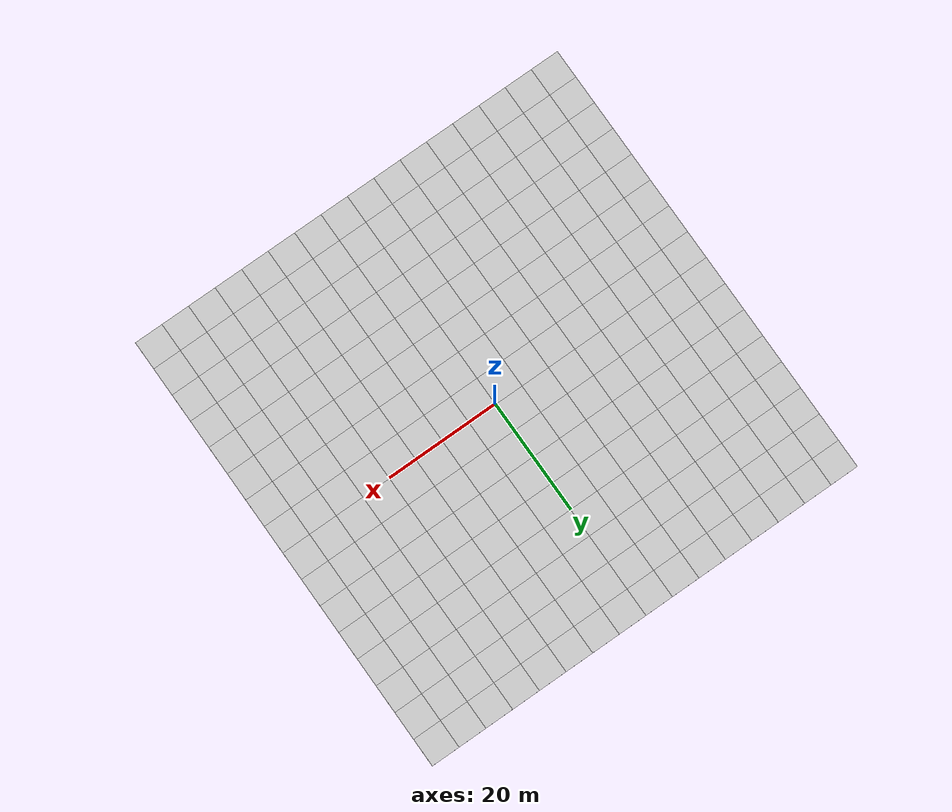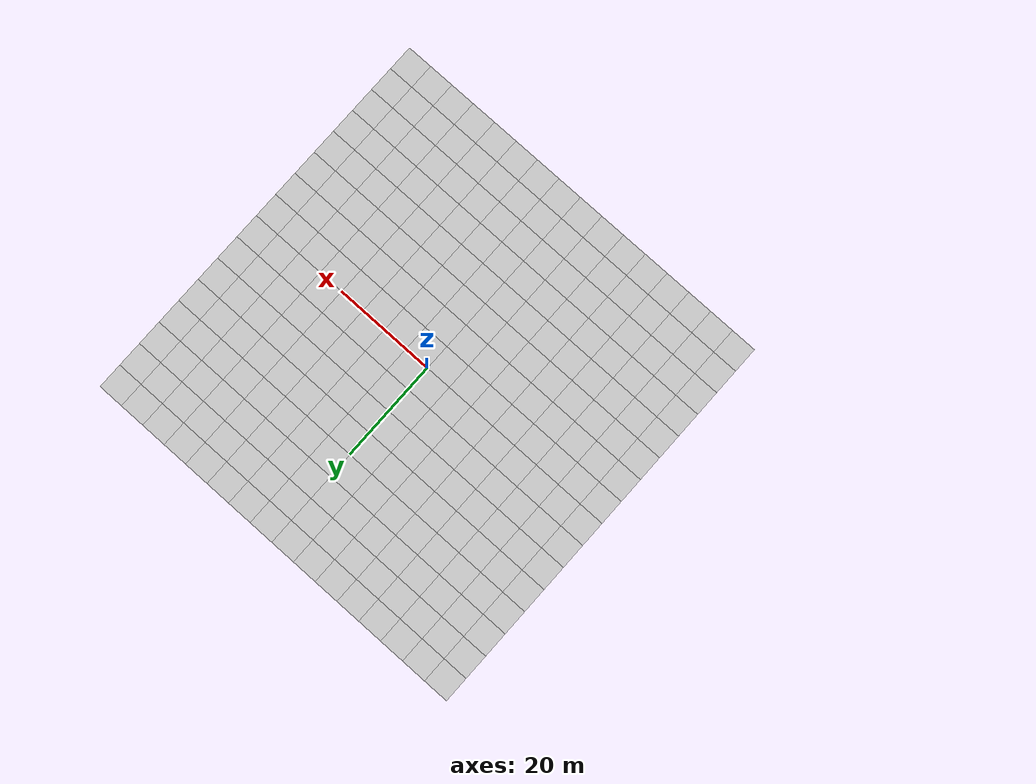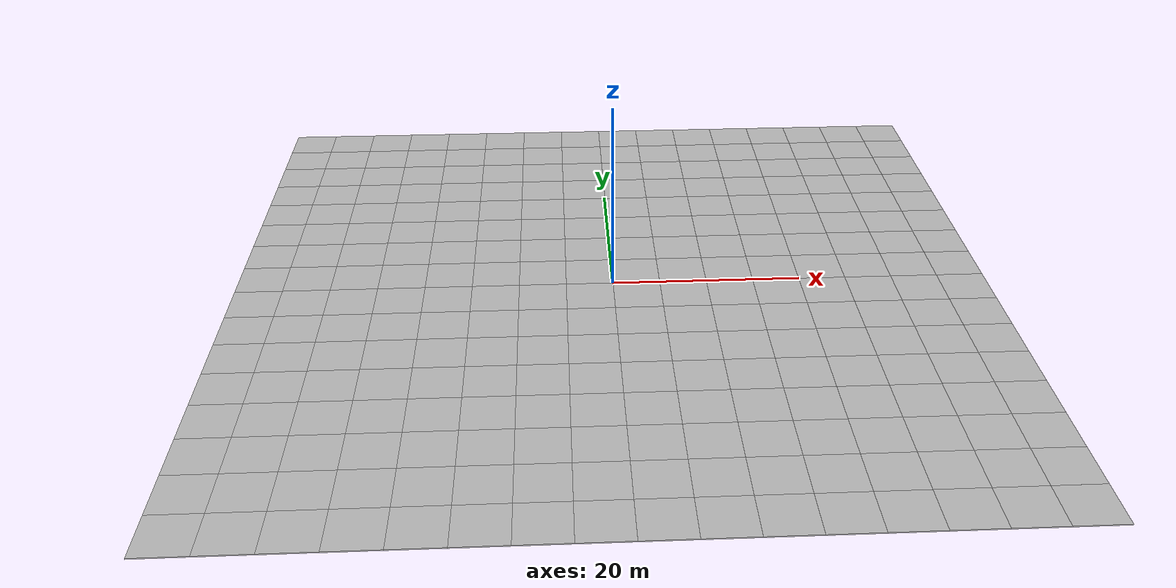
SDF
<?xml version='1.0'?>
<sdf version='1.7'>
  <model name='mud_plane_80x80'>
    <model name='mud_plane_40x40'>
      <model name='mud_plane_20x20'>
        <model name='mud_plane'>
          <static>1</static>
          <link name='link'>
            <collision name='collision'>
              <geometry>
                <box>
                  <size>10 10 0.1</size>
                </box>
              </geometry>
            </collision>
            <visual name='visual_1'>
              <pose>-2.5 2.5 -0.05 0 -0 0</pose>
              <cast_shadows>0</cast_shadows>
              <geometry>
                <box>
                  <size>5 5 0.1</size>
                </box>
              </geometry>
              <material>
                <script>
                  <uri>model://mud_plane/materials/scripts</uri>
                  <uri>model://mud_plane/materials/textures</uri>
                  <name>vrc/mud</name>
                </script>
              </material>
            </visual>
            <visual name='visual_2'>
              <pose>2.5 2.5 -0.05 0 -0 0</pose>
              <cast_shadows>0</cast_shadows>
              <geometry>
                <box>
                  <size>5 5 0.1</size>
                </box>
              </geometry>
              <material>
                <script>
                  <uri>model://mud_plane/materials/scripts</uri>
                  <uri>model://mud_plane/materials/textures</uri>
                  <name>vrc/mud</name>
                </script>
              </material>
            </visual>
            <visual name='visual_3'>
              <pose>2.5 -2.5 -0.05 0 -0 0</pose>
              <cast_shadows>0</cast_shadows>
              <geometry>
                <box>
                  <size>5 5 0.1</size>
                </box>
              </geometry>
              <material>
                <script>
                  <uri>model://mud_plane/materials/scripts</uri>
                  <uri>model://mud_plane/materials/textures</uri>
                  <name>vrc/mud</name>
                </script>
              </material>
            </visual>
            <visual name='visual_4'>
              <pose>-2.5 -2.5 -0.05 0 -0 0</pose>
              <cast_shadows>0</cast_shadows>
              <geometry>
                <box>
                  <size>5 5 0.1</size>
                </box>
              </geometry>
              <material>
                <script>
                  <uri>model://mud_plane/materials/scripts</uri>
                  <uri>model://mud_plane/materials/textures</uri>
                  <name>vrc/mud</name>
                </script>
              </material>
            </visual>
          </link>
          <pose>-4.99986 -4.99991 0 0 -0 0</pose>
        </model>
        <model name='mud_plane_0'>
          <static>1</static>
          <link name='link'>
            <collision name='collision'>
              <geometry>
                <box>
                  <size>10 10 0.1</size>
                </box>
              </geometry>
            </collision>
            <visual name='visual_1'>
              <pose>-2.5 2.5 -0.05 0 -0 0</pose>
              <cast_shadows>0</cast_shadows>
              <geometry>
                <box>
                  <size>5 5 0.1</size>
                </box>
              </geometry>
              <material>
                <script>
                  <uri>model://mud_plane/materials/scripts</uri>
                  <uri>model://mud_plane/materials/textures</uri>
                  <name>vrc/mud</name>
                </script>
              </material>
            </visual>
            <visual name='visual_2'>
              <pose>2.5 2.5 -0.05 0 -0 0</pose>
              <cast_shadows>0</cast_shadows>
              <geometry>
                <box>
                  <size>5 5 0.1</size>
                </box>
              </geometry>
              <material>
                <script>
                  <uri>model://mud_plane/materials/scripts</uri>
                  <uri>model://mud_plane/materials/textures</uri>
                  <name>vrc/mud</name>
                </script>
              </material>
            </visual>
            <visual name='visual_3'>
              <pose>2.5 -2.5 -0.05 0 -0 0</pose>
              <cast_shadows>0</cast_shadows>
              <geometry>
                <box>
                  <size>5 5 0.1</size>
                </box>
              </geometry>
              <material>
                <script>
                  <uri>model://mud_plane/materials/scripts</uri>
                  <uri>model://mud_plane/materials/textures</uri>
                  <name>vrc/mud</name>
                </script>
              </material>
            </visual>
            <visual name='visual_4'>
              <pose>-2.5 -2.5 -0.05 0 -0 0</pose>
              <cast_shadows>0</cast_shadows>
              <geometry>
                <box>
                  <size>5 5 0.1</size>
                </box>
              </geometry>
              <material>
                <script>
                  <uri>model://mud_plane/materials/scripts</uri>
                  <uri>model://mud_plane/materials/textures</uri>
                  <name>vrc/mud</name>
                </script>
              </material>
            </visual>
          </link>
          <pose>-4.99946 4.99954 0 0 -0 0</pose>
        </model>
        <model name='mud_plane_1'>
          <static>1</static>
          <link name='link'>
            <collision name='collision'>
              <geometry>
                <box>
                  <size>10 10 0.1</size>
                </box>
              </geometry>
            </collision>
            <visual name='visual_1'>
              <pose>-2.5 2.5 -0.05 0 -0 0</pose>
              <cast_shadows>0</cast_shadows>
              <geometry>
                <box>
                  <size>5 5 0.1</size>
                </box>
              </geometry>
              <material>
                <script>
                  <uri>model://mud_plane/materials/scripts</uri>
                  <uri>model://mud_plane/materials/textures</uri>
                  <name>vrc/mud</name>
                </script>
              </material>
            </visual>
            <visual name='visual_2'>
              <pose>2.5 2.5 -0.05 0 -0 0</pose>
              <cast_shadows>0</cast_shadows>
              <geometry>
                <box>
                  <size>5 5 0.1</size>
                </box>
              </geometry>
              <material>
                <script>
                  <uri>model://mud_plane/materials/scripts</uri>
                  <uri>model://mud_plane/materials/textures</uri>
                  <name>vrc/mud</name>
                </script>
              </material>
            </visual>
            <visual name='visual_3'>
              <pose>2.5 -2.5 -0.05 0 -0 0</pose>
              <cast_shadows>0</cast_shadows>
              <geometry>
                <box>
                  <size>5 5 0.1</size>
                </box>
              </geometry>
              <material>
                <script>
                  <uri>model://mud_plane/materials/scripts</uri>
                  <uri>model://mud_plane/materials/textures</uri>
                  <name>vrc/mud</name>
                </script>
              </material>
            </visual>
            <visual name='visual_4'>
              <pose>-2.5 -2.5 -0.05 0 -0 0</pose>
              <cast_shadows>0</cast_shadows>
              <geometry>
                <box>
                  <size>5 5 0.1</size>
                </box>
              </geometry>
              <material>
                <script>
                  <uri>model://mud_plane/materials/scripts</uri>
                  <uri>model://mud_plane/materials/textures</uri>
                  <name>vrc/mud</name>
                </script>
              </material>
            </visual>
          </link>
          <pose>4.99964 -4.99949 0 0 -0 0</pose>
        </model>
        <model name='mud_plane_2'>
          <static>1</static>
          <link name='link'>
            <collision name='collision'>
              <geometry>
                <box>
                  <size>10 10 0.1</size>
                </box>
              </geometry>
            </collision>
            <visual name='visual_1'>
              <pose>-2.5 2.5 -0.05 0 -0 0</pose>
              <cast_shadows>0</cast_shadows>
              <geometry>
                <box>
                  <size>5 5 0.1</size>
                </box>
              </geometry>
              <material>
                <script>
                  <uri>model://mud_plane/materials/scripts</uri>
                  <uri>model://mud_plane/materials/textures</uri>
                  <name>vrc/mud</name>
                </script>
              </material>
            </visual>
            <visual name='visual_2'>
              <pose>2.5 2.5 -0.05 0 -0 0</pose>
              <cast_shadows>0</cast_shadows>
              <geometry>
                <box>
                  <size>5 5 0.1</size>
                </box>
              </geometry>
              <material>
                <script>
                  <uri>model://mud_plane/materials/scripts</uri>
                  <uri>model://mud_plane/materials/textures</uri>
                  <name>vrc/mud</name>
                </script>
              </material>
            </visual>
            <visual name='visual_3'>
              <pose>2.5 -2.5 -0.05 0 -0 0</pose>
              <cast_shadows>0</cast_shadows>
              <geometry>
                <box>
                  <size>5 5 0.1</size>
                </box>
              </geometry>
              <material>
                <script>
                  <uri>model://mud_plane/materials/scripts</uri>
                  <uri>model://mud_plane/materials/textures</uri>
                  <name>vrc/mud</name>
                </script>
              </material>
            </visual>
            <visual name='visual_4'>
              <pose>-2.5 -2.5 -0.05 0 -0 0</pose>
              <cast_shadows>0</cast_shadows>
              <geometry>
                <box>
                  <size>5 5 0.1</size>
                </box>
              </geometry>
              <material>
                <script>
                  <uri>model://mud_plane/materials/scripts</uri>
                  <uri>model://mud_plane/materials/textures</uri>
                  <name>vrc/mud</name>
                </script>
              </material>
            </visual>
          </link>
          <pose>4.99967 4.99986 0 0 -0 0</pose>
        </model>
        <static>0</static>
        <allow_auto_disable>1</allow_auto_disable>
        <pose>-9.99895 9.99843 0 0 -0 0</pose>
      </model>
      <model name='mud_plane_20x20_0'>
        <model name='mud_plane'>
          <static>1</static>
          <link name='link'>
            <collision name='collision'>
              <geometry>
                <box>
                  <size>10 10 0.1</size>
                </box>
              </geometry>
            </collision>
            <visual name='visual_1'>
              <pose>-2.5 2.5 -0.05 0 -0 0</pose>
              <cast_shadows>0</cast_shadows>
              <geometry>
                <box>
                  <size>5 5 0.1</size>
                </box>
              </geometry>
              <material>
                <script>
                  <uri>model://mud_plane/materials/scripts</uri>
                  <uri>model://mud_plane/materials/textures</uri>
                  <name>vrc/mud</name>
                </script>
              </material>
            </visual>
            <visual name='visual_2'>
              <pose>2.5 2.5 -0.05 0 -0 0</pose>
              <cast_shadows>0</cast_shadows>
              <geometry>
                <box>
                  <size>5 5 0.1</size>
                </box>
              </geometry>
              <material>
                <script>
                  <uri>model://mud_plane/materials/scripts</uri>
                  <uri>model://mud_plane/materials/textures</uri>
                  <name>vrc/mud</name>
                </script>
              </material>
            </visual>
            <visual name='visual_3'>
              <pose>2.5 -2.5 -0.05 0 -0 0</pose>
              <cast_shadows>0</cast_shadows>
              <geometry>
                <box>
                  <size>5 5 0.1</size>
                </box>
              </geometry>
              <material>
                <script>
                  <uri>model://mud_plane/materials/scripts</uri>
                  <uri>model://mud_plane/materials/textures</uri>
                  <name>vrc/mud</name>
                </script>
              </material>
            </visual>
            <visual name='visual_4'>
              <pose>-2.5 -2.5 -0.05 0 -0 0</pose>
              <cast_shadows>0</cast_shadows>
              <geometry>
                <box>
                  <size>5 5 0.1</size>
                </box>
              </geometry>
              <material>
                <script>
                  <uri>model://mud_plane/materials/scripts</uri>
                  <uri>model://mud_plane/materials/textures</uri>
                  <name>vrc/mud</name>
                </script>
              </material>
            </visual>
          </link>
          <pose>-4.99986 -4.99991 0 0 -0 0</pose>
        </model>
        <model name='mud_plane_0'>
          <static>1</static>
          <link name='link'>
            <collision name='collision'>
              <geometry>
                <box>
                  <size>10 10 0.1</size>
                </box>
              </geometry>
            </collision>
            <visual name='visual_1'>
              <pose>-2.5 2.5 -0.05 0 -0 0</pose>
              <cast_shadows>0</cast_shadows>
              <geometry>
                <box>
                  <size>5 5 0.1</size>
                </box>
              </geometry>
              <material>
                <script>
                  <uri>model://mud_plane/materials/scripts</uri>
                  <uri>model://mud_plane/materials/textures</uri>
                  <name>vrc/mud</name>
                </script>
              </material>
            </visual>
            <visual name='visual_2'>
              <pose>2.5 2.5 -0.05 0 -0 0</pose>
              <cast_shadows>0</cast_shadows>
              <geometry>
                <box>
                  <size>5 5 0.1</size>
                </box>
              </geometry>
              <material>
                <script>
                  <uri>model://mud_plane/materials/scripts</uri>
                  <uri>model://mud_plane/materials/textures</uri>
                  <name>vrc/mud</name>
                </script>
              </material>
            </visual>
            <visual name='visual_3'>
              <pose>2.5 -2.5 -0.05 0 -0 0</pose>
              <cast_shadows>0</cast_shadows>
              <geometry>
                <box>
                  <size>5 5 0.1</size>
                </box>
              </geometry>
              <material>
                <script>
                  <uri>model://mud_plane/materials/scripts</uri>
                  <uri>model://mud_plane/materials/textures</uri>
                  <name>vrc/mud</name>
                </script>
              </material>
            </visual>
            <visual name='visual_4'>
              <pose>-2.5 -2.5 -0.05 0 -0 0</pose>
              <cast_shadows>0</cast_shadows>
              <geometry>
                <box>
                  <size>5 5 0.1</size>
                </box>
              </geometry>
              <material>
                <script>
                  <uri>model://mud_plane/materials/scripts</uri>
                  <uri>model://mud_plane/materials/textures</uri>
                  <name>vrc/mud</name>
                </script>
              </material>
            </visual>
          </link>
          <pose>-4.99946 4.99954 0 0 -0 0</pose>
        </model>
        <model name='mud_plane_1'>
          <static>1</static>
          <link name='link'>
            <collision name='collision'>
              <geometry>
                <box>
                  <size>10 10 0.1</size>
                </box>
              </geometry>
            </collision>
            <visual name='visual_1'>
              <pose>-2.5 2.5 -0.05 0 -0 0</pose>
              <cast_shadows>0</cast_shadows>
              <geometry>
                <box>
                  <size>5 5 0.1</size>
                </box>
              </geometry>
              <material>
                <script>
                  <uri>model://mud_plane/materials/scripts</uri>
                  <uri>model://mud_plane/materials/textures</uri>
                  <name>vrc/mud</name>
                </script>
              </material>
            </visual>
            <visual name='visual_2'>
              <pose>2.5 2.5 -0.05 0 -0 0</pose>
              <cast_shadows>0</cast_shadows>
              <geometry>
                <box>
                  <size>5 5 0.1</size>
                </box>
              </geometry>
              <material>
                <script>
                  <uri>model://mud_plane/materials/scripts</uri>
                  <uri>model://mud_plane/materials/textures</uri>
                  <name>vrc/mud</name>
                </script>
              </material>
            </visual>
            <visual name='visual_3'>
              <pose>2.5 -2.5 -0.05 0 -0 0</pose>
              <cast_shadows>0</cast_shadows>
              <geometry>
                <box>
                  <size>5 5 0.1</size>
                </box>
              </geometry>
              <material>
                <script>
                  <uri>model://mud_plane/materials/scripts</uri>
                  <uri>model://mud_plane/materials/textures</uri>
                  <name>vrc/mud</name>
                </script>
              </material>
            </visual>
            <visual name='visual_4'>
              <pose>-2.5 -2.5 -0.05 0 -0 0</pose>
              <cast_shadows>0</cast_shadows>
              <geometry>
                <box>
                  <size>5 5 0.1</size>
                </box>
              </geometry>
              <material>
                <script>
                  <uri>model://mud_plane/materials/scripts</uri>
                  <uri>model://mud_plane/materials/textures</uri>
                  <name>vrc/mud</name>
                </script>
              </material>
            </visual>
          </link>
          <pose>4.99964 -4.99949 0 0 -0 0</pose>
        </model>
        <model name='mud_plane_2'>
          <static>1</static>
          <link name='link'>
            <collision name='collision'>
              <geometry>
                <box>
                  <size>10 10 0.1</size>
                </box>
              </geometry>
            </collision>
            <visual name='visual_1'>
              <pose>-2.5 2.5 -0.05 0 -0 0</pose>
              <cast_shadows>0</cast_shadows>
              <geometry>
                <box>
                  <size>5 5 0.1</size>
                </box>
              </geometry>
              <material>
                <script>
                  <uri>model://mud_plane/materials/scripts</uri>
                  <uri>model://mud_plane/materials/textures</uri>
                  <name>vrc/mud</name>
                </script>
              </material>
            </visual>
            <visual name='visual_2'>
              <pose>2.5 2.5 -0.05 0 -0 0</pose>
              <cast_shadows>0</cast_shadows>
              <geometry>
                <box>
                  <size>5 5 0.1</size>
                </box>
              </geometry>
              <material>
                <script>
                  <uri>model://mud_plane/materials/scripts</uri>
                  <uri>model://mud_plane/materials/textures</uri>
                  <name>vrc/mud</name>
                </script>
              </material>
            </visual>
            <visual name='visual_3'>
              <pose>2.5 -2.5 -0.05 0 -0 0</pose>
              <cast_shadows>0</cast_shadows>
              <geometry>
                <box>
                  <size>5 5 0.1</size>
                </box>
              </geometry>
              <material>
                <script>
                  <uri>model://mud_plane/materials/scripts</uri>
                  <uri>model://mud_plane/materials/textures</uri>
                  <name>vrc/mud</name>
                </script>
              </material>
            </visual>
            <visual name='visual_4'>
              <pose>-2.5 -2.5 -0.05 0 -0 0</pose>
              <cast_shadows>0</cast_shadows>
              <geometry>
                <box>
                  <size>5 5 0.1</size>
                </box>
              </geometry>
              <material>
                <script>
                  <uri>model://mud_plane/materials/scripts</uri>
                  <uri>model://mud_plane/materials/textures</uri>
                  <name>vrc/mud</name>
                </script>
              </material>
            </visual>
          </link>
          <pose>4.99967 4.99986 0 0 -0 0</pose>
        </model>
        <static>0</static>
        <allow_auto_disable>1</allow_auto_disable>
        <pose>9.99933 9.9997 0 0 -0 0</pose>
      </model>
      <model name='mud_plane_20x20_1'>
        <model name='mud_plane'>
          <static>1</static>
          <link name='link'>
            <collision name='collision'>
              <geometry>
                <box>
                  <size>10 10 0.1</size>
                </box>
              </geometry>
            </collision>
            <visual name='visual_1'>
              <pose>-2.5 2.5 -0.05 0 -0 0</pose>
              <cast_shadows>0</cast_shadows>
              <geometry>
                <box>
                  <size>5 5 0.1</size>
                </box>
              </geometry>
              <material>
                <script>
                  <uri>model://mud_plane/materials/scripts</uri>
                  <uri>model://mud_plane/materials/textures</uri>
                  <name>vrc/mud</name>
                </script>
              </material>
            </visual>
            <visual name='visual_2'>
              <pose>2.5 2.5 -0.05 0 -0 0</pose>
              <cast_shadows>0</cast_shadows>
              <geometry>
                <box>
                  <size>5 5 0.1</size>
                </box>
              </geometry>
              <material>
                <script>
                  <uri>model://mud_plane/materials/scripts</uri>
                  <uri>model://mud_plane/materials/textures</uri>
                  <name>vrc/mud</name>
                </script>
              </material>
            </visual>
            <visual name='visual_3'>
              <pose>2.5 -2.5 -0.05 0 -0 0</pose>
              <cast_shadows>0</cast_shadows>
              <geometry>
                <box>
                  <size>5 5 0.1</size>
                </box>
              </geometry>
              <material>
                <script>
                  <uri>model://mud_plane/materials/scripts</uri>
                  <uri>model://mud_plane/materials/textures</uri>
                  <name>vrc/mud</name>
                </script>
              </material>
            </visual>
            <visual name='visual_4'>
              <pose>-2.5 -2.5 -0.05 0 -0 0</pose>
              <cast_shadows>0</cast_shadows>
              <geometry>
                <box>
                  <size>5 5 0.1</size>
                </box>
              </geometry>
              <material>
                <script>
                  <uri>model://mud_plane/materials/scripts</uri>
                  <uri>model://mud_plane/materials/textures</uri>
                  <name>vrc/mud</name>
                </script>
              </material>
            </visual>
          </link>
          <pose>-4.99986 -4.99991 0 0 -0 0</pose>
        </model>
        <model name='mud_plane_0'>
          <static>1</static>
          <link name='link'>
            <collision name='collision'>
              <geometry>
                <box>
                  <size>10 10 0.1</size>
                </box>
              </geometry>
            </collision>
            <visual name='visual_1'>
              <pose>-2.5 2.5 -0.05 0 -0 0</pose>
              <cast_shadows>0</cast_shadows>
              <geometry>
                <box>
                  <size>5 5 0.1</size>
                </box>
              </geometry>
              <material>
                <script>
                  <uri>model://mud_plane/materials/scripts</uri>
                  <uri>model://mud_plane/materials/textures</uri>
                  <name>vrc/mud</name>
                </script>
              </material>
            </visual>
            <visual name='visual_2'>
              <pose>2.5 2.5 -0.05 0 -0 0</pose>
              <cast_shadows>0</cast_shadows>
              <geometry>
                <box>
                  <size>5 5 0.1</size>
                </box>
              </geometry>
              <material>
                <script>
                  <uri>model://mud_plane/materials/scripts</uri>
                  <uri>model://mud_plane/materials/textures</uri>
                  <name>vrc/mud</name>
                </script>
              </material>
            </visual>
            <visual name='visual_3'>
              <pose>2.5 -2.5 -0.05 0 -0 0</pose>
              <cast_shadows>0</cast_shadows>
              <geometry>
                <box>
                  <size>5 5 0.1</size>
                </box>
              </geometry>
              <material>
                <script>
                  <uri>model://mud_plane/materials/scripts</uri>
                  <uri>model://mud_plane/materials/textures</uri>
                  <name>vrc/mud</name>
                </script>
              </material>
            </visual>
            <visual name='visual_4'>
              <pose>-2.5 -2.5 -0.05 0 -0 0</pose>
              <cast_shadows>0</cast_shadows>
              <geometry>
                <box>
                  <size>5 5 0.1</size>
                </box>
              </geometry>
              <material>
                <script>
                  <uri>model://mud_plane/materials/scripts</uri>
                  <uri>model://mud_plane/materials/textures</uri>
                  <name>vrc/mud</name>
                </script>
              </material>
            </visual>
          </link>
          <pose>-4.99946 4.99954 0 0 -0 0</pose>
        </model>
        <model name='mud_plane_1'>
          <static>1</static>
          <link name='link'>
            <collision name='collision'>
              <geometry>
                <box>
                  <size>10 10 0.1</size>
                </box>
              </geometry>
            </collision>
            <visual name='visual_1'>
              <pose>-2.5 2.5 -0.05 0 -0 0</pose>
              <cast_shadows>0</cast_shadows>
              <geometry>
                <box>
                  <size>5 5 0.1</size>
                </box>
              </geometry>
              <material>
                <script>
                  <uri>model://mud_plane/materials/scripts</uri>
                  <uri>model://mud_plane/materials/textures</uri>
                  <name>vrc/mud</name>
                </script>
              </material>
            </visual>
            <visual name='visual_2'>
              <pose>2.5 2.5 -0.05 0 -0 0</pose>
              <cast_shadows>0</cast_shadows>
              <geometry>
                <box>
                  <size>5 5 0.1</size>
                </box>
              </geometry>
              <material>
                <script>
                  <uri>model://mud_plane/materials/scripts</uri>
                  <uri>model://mud_plane/materials/textures</uri>
                  <name>vrc/mud</name>
                </script>
              </material>
            </visual>
            <visual name='visual_3'>
              <pose>2.5 -2.5 -0.05 0 -0 0</pose>
              <cast_shadows>0</cast_shadows>
              <geometry>
                <box>
                  <size>5 5 0.1</size>
                </box>
              </geometry>
              <material>
                <script>
                  <uri>model://mud_plane/materials/scripts</uri>
                  <uri>model://mud_plane/materials/textures</uri>
                  <name>vrc/mud</name>
                </script>
              </material>
            </visual>
            <visual name='visual_4'>
              <pose>-2.5 -2.5 -0.05 0 -0 0</pose>
              <cast_shadows>0</cast_shadows>
              <geometry>
                <box>
                  <size>5 5 0.1</size>
                </box>
              </geometry>
              <material>
                <script>
                  <uri>model://mud_plane/materials/scripts</uri>
                  <uri>model://mud_plane/materials/textures</uri>
                  <name>vrc/mud</name>
                </script>
              </material>
            </visual>
          </link>
          <pose>4.99964 -4.99949 0 0 -0 0</pose>
        </model>
        <model name='mud_plane_2'>
          <static>1</static>
          <link name='link'>
            <collision name='collision'>
              <geometry>
                <box>
                  <size>10 10 0.1</size>
                </box>
              </geometry>
            </collision>
            <visual name='visual_1'>
              <pose>-2.5 2.5 -0.05 0 -0 0</pose>
              <cast_shadows>0</cast_shadows>
              <geometry>
                <box>
                  <size>5 5 0.1</size>
                </box>
              </geometry>
              <material>
                <script>
                  <uri>model://mud_plane/materials/scripts</uri>
                  <uri>model://mud_plane/materials/textures</uri>
                  <name>vrc/mud</name>
                </script>
              </material>
            </visual>
            <visual name='visual_2'>
              <pose>2.5 2.5 -0.05 0 -0 0</pose>
              <cast_shadows>0</cast_shadows>
              <geometry>
                <box>
                  <size>5 5 0.1</size>
                </box>
              </geometry>
              <material>
                <script>
                  <uri>model://mud_plane/materials/scripts</uri>
                  <uri>model://mud_plane/materials/textures</uri>
                  <name>vrc/mud</name>
                </script>
              </material>
            </visual>
            <visual name='visual_3'>
              <pose>2.5 -2.5 -0.05 0 -0 0</pose>
              <cast_shadows>0</cast_shadows>
              <geometry>
                <box>
                  <size>5 5 0.1</size>
                </box>
              </geometry>
              <material>
                <script>
                  <uri>model://mud_plane/materials/scripts</uri>
                  <uri>model://mud_plane/materials/textures</uri>
                  <name>vrc/mud</name>
                </script>
              </material>
            </visual>
            <visual name='visual_4'>
              <pose>-2.5 -2.5 -0.05 0 -0 0</pose>
              <cast_shadows>0</cast_shadows>
              <geometry>
                <box>
                  <size>5 5 0.1</size>
                </box>
              </geometry>
              <material>
                <script>
                  <uri>model://mud_plane/materials/scripts</uri>
                  <uri>model://mud_plane/materials/textures</uri>
                  <name>vrc/mud</name>
                </script>
              </material>
            </visual>
          </link>
          <pose>4.99967 4.99986 0 0 -0 0</pose>
        </model>
        <static>0</static>
        <allow_auto_disable>1</allow_auto_disable>
        <pose>9.9993 -9.99877 0 0 -0 0</pose>
      </model>
      <model name='mud_plane_20x20_2'>
        <model name='mud_plane'>
          <static>1</static>
          <link name='link'>
            <collision name='collision'>
              <geometry>
                <box>
                  <size>10 10 0.1</size>
                </box>
              </geometry>
            </collision>
            <visual name='visual_1'>
              <pose>-2.5 2.5 -0.05 0 -0 0</pose>
              <cast_shadows>0</cast_shadows>
              <geometry>
                <box>
                  <size>5 5 0.1</size>
                </box>
              </geometry>
              <material>
                <script>
                  <uri>model://mud_plane/materials/scripts</uri>
                  <uri>model://mud_plane/materials/textures</uri>
                  <name>vrc/mud</name>
                </script>
              </material>
            </visual>
            <visual name='visual_2'>
              <pose>2.5 2.5 -0.05 0 -0 0</pose>
              <cast_shadows>0</cast_shadows>
              <geometry>
                <box>
                  <size>5 5 0.1</size>
                </box>
              </geometry>
              <material>
                <script>
                  <uri>model://mud_plane/materials/scripts</uri>
                  <uri>model://mud_plane/materials/textures</uri>
                  <name>vrc/mud</name>
                </script>
              </material>
            </visual>
            <visual name='visual_3'>
              <pose>2.5 -2.5 -0.05 0 -0 0</pose>
              <cast_shadows>0</cast_shadows>
              <geometry>
                <box>
                  <size>5 5 0.1</size>
                </box>
              </geometry>
              <material>
                <script>
                  <uri>model://mud_plane/materials/scripts</uri>
                  <uri>model://mud_plane/materials/textures</uri>
                  <name>vrc/mud</name>
                </script>
              </material>
            </visual>
            <visual name='visual_4'>
              <pose>-2.5 -2.5 -0.05 0 -0 0</pose>
              <cast_shadows>0</cast_shadows>
              <geometry>
                <box>
                  <size>5 5 0.1</size>
                </box>
              </geometry>
              <material>
                <script>
                  <uri>model://mud_plane/materials/scripts</uri>
                  <uri>model://mud_plane/materials/textures</uri>
                  <name>vrc/mud</name>
                </script>
              </material>
            </visual>
          </link>
          <pose>-4.99986 -4.99991 0 0 -0 0</pose>
        </model>
        <model name='mud_plane_0'>
          <static>1</static>
          <link name='link'>
            <collision name='collision'>
              <geometry>
                <box>
                  <size>10 10 0.1</size>
                </box>
              </geometry>
            </collision>
            <visual name='visual_1'>
              <pose>-2.5 2.5 -0.05 0 -0 0</pose>
              <cast_shadows>0</cast_shadows>
              <geometry>
                <box>
                  <size>5 5 0.1</size>
                </box>
              </geometry>
              <material>
                <script>
                  <uri>model://mud_plane/materials/scripts</uri>
                  <uri>model://mud_plane/materials/textures</uri>
                  <name>vrc/mud</name>
                </script>
              </material>
            </visual>
            <visual name='visual_2'>
              <pose>2.5 2.5 -0.05 0 -0 0</pose>
              <cast_shadows>0</cast_shadows>
              <geometry>
                <box>
                  <size>5 5 0.1</size>
                </box>
              </geometry>
              <material>
                <script>
                  <uri>model://mud_plane/materials/scripts</uri>
                  <uri>model://mud_plane/materials/textures</uri>
                  <name>vrc/mud</name>
                </script>
              </material>
            </visual>
            <visual name='visual_3'>
              <pose>2.5 -2.5 -0.05 0 -0 0</pose>
              <cast_shadows>0</cast_shadows>
              <geometry>
                <box>
                  <size>5 5 0.1</size>
                </box>
              </geometry>
              <material>
                <script>
                  <uri>model://mud_plane/materials/scripts</uri>
                  <uri>model://mud_plane/materials/textures</uri>
                  <name>vrc/mud</name>
                </script>
              </material>
            </visual>
            <visual name='visual_4'>
              <pose>-2.5 -2.5 -0.05 0 -0 0</pose>
              <cast_shadows>0</cast_shadows>
              <geometry>
                <box>
                  <size>5 5 0.1</size>
                </box>
              </geometry>
              <material>
                <script>
                  <uri>model://mud_plane/materials/scripts</uri>
                  <uri>model://mud_plane/materials/textures</uri>
                  <name>vrc/mud</name>
                </script>
              </material>
            </visual>
          </link>
          <pose>-4.99946 4.99954 0 0 -0 0</pose>
        </model>
        <model name='mud_plane_1'>
          <static>1</static>
          <link name='link'>
            <collision name='collision'>
              <geometry>
                <box>
                  <size>10 10 0.1</size>
                </box>
              </geometry>
            </collision>
            <visual name='visual_1'>
              <pose>-2.5 2.5 -0.05 0 -0 0</pose>
              <cast_shadows>0</cast_shadows>
              <geometry>
                <box>
                  <size>5 5 0.1</size>
                </box>
              </geometry>
              <material>
                <script>
                  <uri>model://mud_plane/materials/scripts</uri>
                  <uri>model://mud_plane/materials/textures</uri>
                  <name>vrc/mud</name>
                </script>
              </material>
            </visual>
            <visual name='visual_2'>
              <pose>2.5 2.5 -0.05 0 -0 0</pose>
              <cast_shadows>0</cast_shadows>
              <geometry>
                <box>
                  <size>5 5 0.1</size>
                </box>
              </geometry>
              <material>
                <script>
                  <uri>model://mud_plane/materials/scripts</uri>
                  <uri>model://mud_plane/materials/textures</uri>
                  <name>vrc/mud</name>
                </script>
              </material>
            </visual>
            <visual name='visual_3'>
              <pose>2.5 -2.5 -0.05 0 -0 0</pose>
              <cast_shadows>0</cast_shadows>
              <geometry>
                <box>
                  <size>5 5 0.1</size>
                </box>
              </geometry>
              <material>
                <script>
                  <uri>model://mud_plane/materials/scripts</uri>
                  <uri>model://mud_plane/materials/textures</uri>
                  <name>vrc/mud</name>
                </script>
              </material>
            </visual>
            <visual name='visual_4'>
              <pose>-2.5 -2.5 -0.05 0 -0 0</pose>
              <cast_shadows>0</cast_shadows>
              <geometry>
                <box>
                  <size>5 5 0.1</size>
                </box>
              </geometry>
              <material>
                <script>
                  <uri>model://mud_plane/materials/scripts</uri>
                  <uri>model://mud_plane/materials/textures</uri>
                  <name>vrc/mud</name>
                </script>
              </material>
            </visual>
          </link>
          <pose>4.99964 -4.99949 0 0 -0 0</pose>
        </model>
        <model name='mud_plane_2'>
          <static>1</static>
          <link name='link'>
            <collision name='collision'>
              <geometry>
                <box>
                  <size>10 10 0.1</size>
                </box>
              </geometry>
            </collision>
            <visual name='visual_1'>
              <pose>-2.5 2.5 -0.05 0 -0 0</pose>
              <cast_shadows>0</cast_shadows>
              <geometry>
                <box>
                  <size>5 5 0.1</size>
                </box>
              </geometry>
              <material>
                <script>
                  <uri>model://mud_plane/materials/scripts</uri>
                  <uri>model://mud_plane/materials/textures</uri>
                  <name>vrc/mud</name>
                </script>
              </material>
            </visual>
            <visual name='visual_2'>
              <pose>2.5 2.5 -0.05 0 -0 0</pose>
              <cast_shadows>0</cast_shadows>
              <geometry>
                <box>
                  <size>5 5 0.1</size>
                </box>
              </geometry>
              <material>
                <script>
                  <uri>model://mud_plane/materials/scripts</uri>
                  <uri>model://mud_plane/materials/textures</uri>
                  <name>vrc/mud</name>
                </script>
              </material>
            </visual>
            <visual name='visual_3'>
              <pose>2.5 -2.5 -0.05 0 -0 0</pose>
              <cast_shadows>0</cast_shadows>
              <geometry>
                <box>
                  <size>5 5 0.1</size>
                </box>
              </geometry>
              <material>
                <script>
                  <uri>model://mud_plane/materials/scripts</uri>
                  <uri>model://mud_plane/materials/textures</uri>
                  <name>vrc/mud</name>
                </script>
              </material>
            </visual>
            <visual name='visual_4'>
              <pose>-2.5 -2.5 -0.05 0 -0 0</pose>
              <cast_shadows>0</cast_shadows>
              <geometry>
                <box>
                  <size>5 5 0.1</size>
                </box>
              </geometry>
              <material>
                <script>
                  <uri>model://mud_plane/materials/scripts</uri>
                  <uri>model://mud_plane/materials/textures</uri>
                  <name>vrc/mud</name>
                </script>
              </material>
            </visual>
          </link>
          <pose>4.99967 4.99986 0 0 -0 0</pose>
        </model>
        <static>0</static>
        <allow_auto_disable>1</allow_auto_disable>
        <pose>-9.99969 -9.99935 0 0 -0 0</pose>
      </model>
      <static>0</static>
      <allow_auto_disable>1</allow_auto_disable>
      <pose>19.9986 19.9995 0 0 -0 0</pose>
    </model>
    <model name='mud_plane_40x40_0'>
      <model name='mud_plane_20x20'>
        <model name='mud_plane'>
          <static>1</static>
          <link name='link'>
            <collision name='collision'>
              <geometry>
                <box>
                  <size>10 10 0.1</size>
                </box>
              </geometry>
            </collision>
            <visual name='visual_1'>
              <pose>-2.5 2.5 -0.05 0 -0 0</pose>
              <cast_shadows>0</cast_shadows>
              <geometry>
                <box>
                  <size>5 5 0.1</size>
                </box>
              </geometry>
              <material>
                <script>
                  <uri>model://mud_plane/materials/scripts</uri>
                  <uri>model://mud_plane/materials/textures</uri>
                  <name>vrc/mud</name>
                </script>
              </material>
            </visual>
            <visual name='visual_2'>
              <pose>2.5 2.5 -0.05 0 -0 0</pose>
              <cast_shadows>0</cast_shadows>
              <geometry>
                <box>
                  <size>5 5 0.1</size>
                </box>
              </geometry>
              <material>
                <script>
                  <uri>model://mud_plane/materials/scripts</uri>
                  <uri>model://mud_plane/materials/textures</uri>
                  <name>vrc/mud</name>
                </script>
              </material>
            </visual>
            <visual name='visual_3'>
              <pose>2.5 -2.5 -0.05 0 -0 0</pose>
              <cast_shadows>0</cast_shadows>
              <geometry>
                <box>
                  <size>5 5 0.1</size>
                </box>
              </geometry>
              <material>
                <script>
                  <uri>model://mud_plane/materials/scripts</uri>
                  <uri>model://mud_plane/materials/textures</uri>
                  <name>vrc/mud</name>
                </script>
              </material>
            </visual>
            <visual name='visual_4'>
              <pose>-2.5 -2.5 -0.05 0 -0 0</pose>
              <cast_shadows>0</cast_shadows>
              <geometry>
                <box>
                  <size>5 5 0.1</size>
                </box>
              </geometry>
              <material>
                <script>
                  <uri>model://mud_plane/materials/scripts</uri>
                  <uri>model://mud_plane/materials/textures</uri>
                  <name>vrc/mud</name>
                </script>
              </material>
            </visual>
          </link>
          <pose>-4.99986 -4.99991 0 0 -0 0</pose>
        </model>
        <model name='mud_plane_0'>
          <static>1</static>
          <link name='link'>
            <collision name='collision'>
              <geometry>
                <box>
                  <size>10 10 0.1</size>
                </box>
              </geometry>
            </collision>
            <visual name='visual_1'>
              <pose>-2.5 2.5 -0.05 0 -0 0</pose>
              <cast_shadows>0</cast_shadows>
              <geometry>
                <box>
                  <size>5 5 0.1</size>
                </box>
              </geometry>
              <material>
                <script>
                  <uri>model://mud_plane/materials/scripts</uri>
                  <uri>model://mud_plane/materials/textures</uri>
                  <name>vrc/mud</name>
                </script>
              </material>
            </visual>
            <visual name='visual_2'>
              <pose>2.5 2.5 -0.05 0 -0 0</pose>
              <cast_shadows>0</cast_shadows>
              <geometry>
                <box>
                  <size>5 5 0.1</size>
                </box>
              </geometry>
              <material>
                <script>
                  <uri>model://mud_plane/materials/scripts</uri>
                  <uri>model://mud_plane/materials/textures</uri>
                  <name>vrc/mud</name>
                </script>
              </material>
            </visual>
            <visual name='visual_3'>
              <pose>2.5 -2.5 -0.05 0 -0 0</pose>
              <cast_shadows>0</cast_shadows>
              <geometry>
                <box>
                  <size>5 5 0.1</size>
                </box>
              </geometry>
              <material>
                <script>
                  <uri>model://mud_plane/materials/scripts</uri>
                  <uri>model://mud_plane/materials/textures</uri>
                  <name>vrc/mud</name>
                </script>
              </material>
            </visual>
            <visual name='visual_4'>
              <pose>-2.5 -2.5 -0.05 0 -0 0</pose>
              <cast_shadows>0</cast_shadows>
              <geometry>
                <box>
                  <size>5 5 0.1</size>
                </box>
              </geometry>
              <material>
                <script>
                  <uri>model://mud_plane/materials/scripts</uri>
                  <uri>model://mud_plane/materials/textures</uri>
                  <name>vrc/mud</name>
                </script>
              </material>
            </visual>
          </link>
          <pose>-4.99946 4.99954 0 0 -0 0</pose>
        </model>
        <model name='mud_plane_1'>
          <static>1</static>
          <link name='link'>
            <collision name='collision'>
              <geometry>
                <box>
                  <size>10 10 0.1</size>
                </box>
              </geometry>
            </collision>
            <visual name='visual_1'>
              <pose>-2.5 2.5 -0.05 0 -0 0</pose>
              <cast_shadows>0</cast_shadows>
              <geometry>
                <box>
                  <size>5 5 0.1</size>
                </box>
              </geometry>
              <material>
                <script>
                  <uri>model://mud_plane/materials/scripts</uri>
                  <uri>model://mud_plane/materials/textures</uri>
                  <name>vrc/mud</name>
                </script>
              </material>
            </visual>
            <visual name='visual_2'>
              <pose>2.5 2.5 -0.05 0 -0 0</pose>
              <cast_shadows>0</cast_shadows>
              <geometry>
                <box>
                  <size>5 5 0.1</size>
                </box>
              </geometry>
              <material>
                <script>
                  <uri>model://mud_plane/materials/scripts</uri>
                  <uri>model://mud_plane/materials/textures</uri>
                  <name>vrc/mud</name>
                </script>
              </material>
            </visual>
            <visual name='visual_3'>
              <pose>2.5 -2.5 -0.05 0 -0 0</pose>
              <cast_shadows>0</cast_shadows>
              <geometry>
                <box>
                  <size>5 5 0.1</size>
                </box>
              </geometry>
              <material>
                <script>
                  <uri>model://mud_plane/materials/scripts</uri>
                  <uri>model://mud_plane/materials/textures</uri>
                  <name>vrc/mud</name>
                </script>
              </material>
            </visual>
            <visual name='visual_4'>
              <pose>-2.5 -2.5 -0.05 0 -0 0</pose>
              <cast_shadows>0</cast_shadows>
              <geometry>
                <box>
                  <size>5 5 0.1</size>
                </box>
              </geometry>
              <material>
                <script>
                  <uri>model://mud_plane/materials/scripts</uri>
                  <uri>model://mud_plane/materials/textures</uri>
                  <name>vrc/mud</name>
                </script>
              </material>
            </visual>
          </link>
          <pose>4.99964 -4.99949 0 0 -0 0</pose>
        </model>
        <model name='mud_plane_2'>
          <static>1</static>
          <link name='link'>
            <collision name='collision'>
              <geometry>
                <box>
                  <size>10 10 0.1</size>
                </box>
              </geometry>
            </collision>
            <visual name='visual_1'>
              <pose>-2.5 2.5 -0.05 0 -0 0</pose>
              <cast_shadows>0</cast_shadows>
              <geometry>
                <box>
                  <size>5 5 0.1</size>
                </box>
              </geometry>
              <material>
                <script>
                  <uri>model://mud_plane/materials/scripts</uri>
                  <uri>model://mud_plane/materials/textures</uri>
                  <name>vrc/mud</name>
                </script>
              </material>
            </visual>
            <visual name='visual_2'>
              <pose>2.5 2.5 -0.05 0 -0 0</pose>
              <cast_shadows>0</cast_shadows>
              <geometry>
                <box>
                  <size>5 5 0.1</size>
                </box>
              </geometry>
              <material>
                <script>
                  <uri>model://mud_plane/materials/scripts</uri>
                  <uri>model://mud_plane/materials/textures</uri>
                  <name>vrc/mud</name>
                </script>
              </material>
            </visual>
            <visual name='visual_3'>
              <pose>2.5 -2.5 -0.05 0 -0 0</pose>
              <cast_shadows>0</cast_shadows>
              <geometry>
                <box>
                  <size>5 5 0.1</size>
                </box>
              </geometry>
              <material>
                <script>
                  <uri>model://mud_plane/materials/scripts</uri>
                  <uri>model://mud_plane/materials/textures</uri>
                  <name>vrc/mud</name>
                </script>
              </material>
            </visual>
            <visual name='visual_4'>
              <pose>-2.5 -2.5 -0.05 0 -0 0</pose>
              <cast_shadows>0</cast_shadows>
              <geometry>
                <box>
                  <size>5 5 0.1</size>
                </box>
              </geometry>
              <material>
                <script>
                  <uri>model://mud_plane/materials/scripts</uri>
                  <uri>model://mud_plane/materials/textures</uri>
                  <name>vrc/mud</name>
                </script>
              </material>
            </visual>
          </link>
          <pose>4.99967 4.99986 0 0 -0 0</pose>
        </model>
        <static>0</static>
        <allow_auto_disable>1</allow_auto_disable>
        <pose>-9.99895 9.99843 0 0 -0 0</pose>
      </model>
      <model name='mud_plane_20x20_0'>
        <model name='mud_plane'>
          <static>1</static>
          <link name='link'>
            <collision name='collision'>
              <geometry>
                <box>
                  <size>10 10 0.1</size>
                </box>
              </geometry>
            </collision>
            <visual name='visual_1'>
              <pose>-2.5 2.5 -0.05 0 -0 0</pose>
              <cast_shadows>0</cast_shadows>
              <geometry>
                <box>
                  <size>5 5 0.1</size>
                </box>
              </geometry>
              <material>
                <script>
                  <uri>model://mud_plane/materials/scripts</uri>
                  <uri>model://mud_plane/materials/textures</uri>
                  <name>vrc/mud</name>
                </script>
              </material>
            </visual>
            <visual name='visual_2'>
              <pose>2.5 2.5 -0.05 0 -0 0</pose>
              <cast_shadows>0</cast_shadows>
              <geometry>
                <box>
                  <size>5 5 0.1</size>
                </box>
              </geometry>
              <material>
                <script>
                  <uri>model://mud_plane/materials/scripts</uri>
                  <uri>model://mud_plane/materials/textures</uri>
                  <name>vrc/mud</name>
                </script>
              </material>
            </visual>
            <visual name='visual_3'>
              <pose>2.5 -2.5 -0.05 0 -0 0</pose>
              <cast_shadows>0</cast_shadows>
              <geometry>
                <box>
                  <size>5 5 0.1</size>
                </box>
              </geometry>
              <material>
                <script>
                  <uri>model://mud_plane/materials/scripts</uri>
                  <uri>model://mud_plane/materials/textures</uri>
                  <name>vrc/mud</name>
                </script>
              </material>
            </visual>
            <visual name='visual_4'>
              <pose>-2.5 -2.5 -0.05 0 -0 0</pose>
              <cast_shadows>0</cast_shadows>
              <geometry>
                <box>
                  <size>5 5 0.1</size>
                </box>
              </geometry>
              <material>
                <script>
                  <uri>model://mud_plane/materials/scripts</uri>
                  <uri>model://mud_plane/materials/textures</uri>
                  <name>vrc/mud</name>
                </script>
              </material>
            </visual>
          </link>
          <pose>-4.99986 -4.99991 0 0 -0 0</pose>
        </model>
        <model name='mud_plane_0'>
          <static>1</static>
          <link name='link'>
            <collision name='collision'>
              <geometry>
                <box>
                  <size>10 10 0.1</size>
                </box>
              </geometry>
            </collision>
            <visual name='visual_1'>
              <pose>-2.5 2.5 -0.05 0 -0 0</pose>
              <cast_shadows>0</cast_shadows>
              <geometry>
                <box>
                  <size>5 5 0.1</size>
                </box>
              </geometry>
              <material>
                <script>
                  <uri>model://mud_plane/materials/scripts</uri>
                  <uri>model://mud_plane/materials/textures</uri>
                  <name>vrc/mud</name>
                </script>
              </material>
            </visual>
            <visual name='visual_2'>
              <pose>2.5 2.5 -0.05 0 -0 0</pose>
              <cast_shadows>0</cast_shadows>
              <geometry>
                <box>
                  <size>5 5 0.1</size>
                </box>
              </geometry>
              <material>
                <script>
                  <uri>model://mud_plane/materials/scripts</uri>
                  <uri>model://mud_plane/materials/textures</uri>
                  <name>vrc/mud</name>
                </script>
              </material>
            </visual>
            <visual name='visual_3'>
              <pose>2.5 -2.5 -0.05 0 -0 0</pose>
              <cast_shadows>0</cast_shadows>
              <geometry>
                <box>
                  <size>5 5 0.1</size>
                </box>
              </geometry>
              <material>
                <script>
                  <uri>model://mud_plane/materials/scripts</uri>
                  <uri>model://mud_plane/materials/textures</uri>
                  <name>vrc/mud</name>
                </script>
              </material>
            </visual>
            <visual name='visual_4'>
              <pose>-2.5 -2.5 -0.05 0 -0 0</pose>
              <cast_shadows>0</cast_shadows>
              <geometry>
                <box>
                  <size>5 5 0.1</size>
                </box>
              </geometry>
              <material>
                <script>
                  <uri>model://mud_plane/materials/scripts</uri>
                  <uri>model://mud_plane/materials/textures</uri>
                  <name>vrc/mud</name>
                </script>
              </material>
            </visual>
          </link>
          <pose>-4.99946 4.99954 0 0 -0 0</pose>
        </model>
        <model name='mud_plane_1'>
          <static>1</static>
          <link name='link'>
            <collision name='collision'>
              <geometry>
                <box>
                  <size>10 10 0.1</size>
                </box>
              </geometry>
            </collision>
            <visual name='visual_1'>
              <pose>-2.5 2.5 -0.05 0 -0 0</pose>
              <cast_shadows>0</cast_shadows>
              <geometry>
                <box>
                  <size>5 5 0.1</size>
                </box>
              </geometry>
              <material>
                <script>
                  <uri>model://mud_plane/materials/scripts</uri>
                  <uri>model://mud_plane/materials/textures</uri>
                  <name>vrc/mud</name>
                </script>
              </material>
            </visual>
            <visual name='visual_2'>
              <pose>2.5 2.5 -0.05 0 -0 0</pose>
              <cast_shadows>0</cast_shadows>
              <geometry>
                <box>
                  <size>5 5 0.1</size>
                </box>
              </geometry>
              <material>
                <script>
                  <uri>model://mud_plane/materials/scripts</uri>
                  <uri>model://mud_plane/materials/textures</uri>
                  <name>vrc/mud</name>
                </script>
              </material>
            </visual>
            <visual name='visual_3'>
              <pose>2.5 -2.5 -0.05 0 -0 0</pose>
              <cast_shadows>0</cast_shadows>
              <geometry>
                <box>
                  <size>5 5 0.1</size>
                </box>
              </geometry>
              <material>
                <script>
                  <uri>model://mud_plane/materials/scripts</uri>
                  <uri>model://mud_plane/materials/textures</uri>
                  <name>vrc/mud</name>
                </script>
              </material>
            </visual>
            <visual name='visual_4'>
              <pose>-2.5 -2.5 -0.05 0 -0 0</pose>
              <cast_shadows>0</cast_shadows>
              <geometry>
                <box>
                  <size>5 5 0.1</size>
                </box>
              </geometry>
              <material>
                <script>
                  <uri>model://mud_plane/materials/scripts</uri>
                  <uri>model://mud_plane/materials/textures</uri>
                  <name>vrc/mud</name>
                </script>
              </material>
            </visual>
          </link>
          <pose>4.99964 -4.99949 0 0 -0 0</pose>
        </model>
        <model name='mud_plane_2'>
          <static>1</static>
          <link name='link'>
            <collision name='collision'>
              <geometry>
                <box>
                  <size>10 10 0.1</size>
                </box>
              </geometry>
            </collision>
            <visual name='visual_1'>
              <pose>-2.5 2.5 -0.05 0 -0 0</pose>
              <cast_shadows>0</cast_shadows>
              <geometry>
                <box>
                  <size>5 5 0.1</size>
                </box>
              </geometry>
              <material>
                <script>
                  <uri>model://mud_plane/materials/scripts</uri>
                  <uri>model://mud_plane/materials/textures</uri>
                  <name>vrc/mud</name>
                </script>
              </material>
            </visual>
            <visual name='visual_2'>
              <pose>2.5 2.5 -0.05 0 -0 0</pose>
              <cast_shadows>0</cast_shadows>
              <geometry>
                <box>
                  <size>5 5 0.1</size>
                </box>
              </geometry>
              <material>
                <script>
                  <uri>model://mud_plane/materials/scripts</uri>
                  <uri>model://mud_plane/materials/textures</uri>
                  <name>vrc/mud</name>
                </script>
              </material>
            </visual>
            <visual name='visual_3'>
              <pose>2.5 -2.5 -0.05 0 -0 0</pose>
              <cast_shadows>0</cast_shadows>
              <geometry>
                <box>
                  <size>5 5 0.1</size>
                </box>
              </geometry>
              <material>
                <script>
                  <uri>model://mud_plane/materials/scripts</uri>
                  <uri>model://mud_plane/materials/textures</uri>
                  <name>vrc/mud</name>
                </script>
              </material>
            </visual>
            <visual name='visual_4'>
              <pose>-2.5 -2.5 -0.05 0 -0 0</pose>
              <cast_shadows>0</cast_shadows>
              <geometry>
                <box>
                  <size>5 5 0.1</size>
                </box>
              </geometry>
              <material>
                <script>
                  <uri>model://mud_plane/materials/scripts</uri>
                  <uri>model://mud_plane/materials/textures</uri>
                  <name>vrc/mud</name>
                </script>
              </material>
            </visual>
          </link>
          <pose>4.99967 4.99986 0 0 -0 0</pose>
        </model>
        <static>0</static>
        <allow_auto_disable>1</allow_auto_disable>
        <pose>9.99933 9.9997 0 0 -0 0</pose>
      </model>
      <model name='mud_plane_20x20_1'>
        <model name='mud_plane'>
          <static>1</static>
          <link name='link'>
            <collision name='collision'>
              <geometry>
                <box>
                  <size>10 10 0.1</size>
                </box>
              </geometry>
            </collision>
            <visual name='visual_1'>
              <pose>-2.5 2.5 -0.05 0 -0 0</pose>
              <cast_shadows>0</cast_shadows>
              <geometry>
                <box>
                  <size>5 5 0.1</size>
                </box>
              </geometry>
              <material>
                <script>
                  <uri>model://mud_plane/materials/scripts</uri>
                  <uri>model://mud_plane/materials/textures</uri>
                  <name>vrc/mud</name>
                </script>
              </material>
            </visual>
            <visual name='visual_2'>
              <pose>2.5 2.5 -0.05 0 -0 0</pose>
              <cast_shadows>0</cast_shadows>
              <geometry>
                <box>
                  <size>5 5 0.1</size>
                </box>
              </geometry>
              <material>
                <script>
                  <uri>model://mud_plane/materials/scripts</uri>
                  <uri>model://mud_plane/materials/textures</uri>
                  <name>vrc/mud</name>
                </script>
              </material>
            </visual>
            <visual name='visual_3'>
              <pose>2.5 -2.5 -0.05 0 -0 0</pose>
              <cast_shadows>0</cast_shadows>
              <geometry>
                <box>
                  <size>5 5 0.1</size>
                </box>
              </geometry>
              <material>
                <script>
                  <uri>model://mud_plane/materials/scripts</uri>
                  <uri>model://mud_plane/materials/textures</uri>
                  <name>vrc/mud</name>
                </script>
              </material>
            </visual>
            <visual name='visual_4'>
              <pose>-2.5 -2.5 -0.05 0 -0 0</pose>
              <cast_shadows>0</cast_shadows>
              <geometry>
                <box>
                  <size>5 5 0.1</size>
                </box>
              </geometry>
              <material>
                <script>
                  <uri>model://mud_plane/materials/scripts</uri>
                  <uri>model://mud_plane/materials/textures</uri>
                  <name>vrc/mud</name>
                </script>
              </material>
            </visual>
          </link>
          <pose>-4.99986 -4.99991 0 0 -0 0</pose>
        </model>
        <model name='mud_plane_0'>
          <static>1</static>
          <link name='link'>
            <collision name='collision'>
              <geometry>
                <box>
                  <size>10 10 0.1</size>
                </box>
              </geometry>
            </collision>
            <visual name='visual_1'>
              <pose>-2.5 2.5 -0.05 0 -0 0</pose>
              <cast_shadows>0</cast_shadows>
              <geometry>
                <box>
                  <size>5 5 0.1</size>
                </box>
              </geometry>
              <material>
                <script>
                  <uri>model://mud_plane/materials/scripts</uri>
                  <uri>model://mud_plane/materials/textures</uri>
                  <name>vrc/mud</name>
                </script>
              </material>
            </visual>
            <visual name='visual_2'>
              <pose>2.5 2.5 -0.05 0 -0 0</pose>
              <cast_shadows>0</cast_shadows>
              <geometry>
                <box>
                  <size>5 5 0.1</size>
                </box>
              </geometry>
              <material>
                <script>
                  <uri>model://mud_plane/materials/scripts</uri>
                  <uri>model://mud_plane/materials/textures</uri>
                  <name>vrc/mud</name>
                </script>
              </material>
            </visual>
            <visual name='visual_3'>
              <pose>2.5 -2.5 -0.05 0 -0 0</pose>
              <cast_shadows>0</cast_shadows>
              <geometry>
                <box>
                  <size>5 5 0.1</size>
                </box>
              </geometry>
              <material>
                <script>
                  <uri>model://mud_plane/materials/scripts</uri>
                  <uri>model://mud_plane/materials/textures</uri>
                  <name>vrc/mud</name>
                </script>
              </material>
            </visual>
            <visual name='visual_4'>
              <pose>-2.5 -2.5 -0.05 0 -0 0</pose>
              <cast_shadows>0</cast_shadows>
              <geometry>
                <box>
                  <size>5 5 0.1</size>
                </box>
              </geometry>
              <material>
                <script>
                  <uri>model://mud_plane/materials/scripts</uri>
                  <uri>model://mud_plane/materials/textures</uri>
                  <name>vrc/mud</name>
                </script>
              </material>
            </visual>
          </link>
          <pose>-4.99946 4.99954 0 0 -0 0</pose>
        </model>
        <model name='mud_plane_1'>
          <static>1</static>
          <link name='link'>
            <collision name='collision'>
              <geometry>
                <box>
                  <size>10 10 0.1</size>
                </box>
              </geometry>
            </collision>
            <visual name='visual_1'>
              <pose>-2.5 2.5 -0.05 0 -0 0</pose>
              <cast_shadows>0</cast_shadows>
              <geometry>
                <box>
                  <size>5 5 0.1</size>
                </box>
              </geometry>
              <material>
                <script>
                  <uri>model://mud_plane/materials/scripts</uri>
                  <uri>model://mud_plane/materials/textures</uri>
                  <name>vrc/mud</name>
                </script>
              </material>
            </visual>
            <visual name='visual_2'>
              <pose>2.5 2.5 -0.05 0 -0 0</pose>
              <cast_shadows>0</cast_shadows>
              <geometry>
                <box>
                  <size>5 5 0.1</size>
                </box>
              </geometry>
              <material>
                <script>
                  <uri>model://mud_plane/materials/scripts</uri>
                  <uri>model://mud_plane/materials/textures</uri>
                  <name>vrc/mud</name>
                </script>
              </material>
            </visual>
            <visual name='visual_3'>
              <pose>2.5 -2.5 -0.05 0 -0 0</pose>
              <cast_shadows>0</cast_shadows>
              <geometry>
                <box>
                  <size>5 5 0.1</size>
                </box>
              </geometry>
              <material>
                <script>
                  <uri>model://mud_plane/materials/scripts</uri>
                  <uri>model://mud_plane/materials/textures</uri>
                  <name>vrc/mud</name>
                </script>
              </material>
            </visual>
            <visual name='visual_4'>
              <pose>-2.5 -2.5 -0.05 0 -0 0</pose>
              <cast_shadows>0</cast_shadows>
              <geometry>
                <box>
                  <size>5 5 0.1</size>
                </box>
              </geometry>
              <material>
                <script>
                  <uri>model://mud_plane/materials/scripts</uri>
                  <uri>model://mud_plane/materials/textures</uri>
                  <name>vrc/mud</name>
                </script>
              </material>
            </visual>
          </link>
          <pose>4.99964 -4.99949 0 0 -0 0</pose>
        </model>
        <model name='mud_plane_2'>
          <static>1</static>
          <link name='link'>
            <collision name='collision'>
              <geometry>
                <box>
                  <size>10 10 0.1</size>
                </box>
              </geometry>
            </collision>
            <visual name='visual_1'>
              <pose>-2.5 2.5 -0.05 0 -0 0</pose>
              <cast_shadows>0</cast_shadows>
              <geometry>
                <box>
                  <size>5 5 0.1</size>
                </box>
              </geometry>
              <material>
                <script>
                  <uri>model://mud_plane/materials/scripts</uri>
                  <uri>model://mud_plane/materials/textures</uri>
                  <name>vrc/mud</name>
                </script>
              </material>
            </visual>
            <visual name='visual_2'>
              <pose>2.5 2.5 -0.05 0 -0 0</pose>
              <cast_shadows>0</cast_shadows>
              <geometry>
                <box>
                  <size>5 5 0.1</size>
                </box>
              </geometry>
              <material>
                <script>
                  <uri>model://mud_plane/materials/scripts</uri>
                  <uri>model://mud_plane/materials/textures</uri>
                  <name>vrc/mud</name>
                </script>
              </material>
            </visual>
            <visual name='visual_3'>
              <pose>2.5 -2.5 -0.05 0 -0 0</pose>
              <cast_shadows>0</cast_shadows>
              <geometry>
                <box>
                  <size>5 5 0.1</size>
                </box>
              </geometry>
              <material>
                <script>
                  <uri>model://mud_plane/materials/scripts</uri>
                  <uri>model://mud_plane/materials/textures</uri>
                  <name>vrc/mud</name>
                </script>
              </material>
            </visual>
            <visual name='visual_4'>
              <pose>-2.5 -2.5 -0.05 0 -0 0</pose>
              <cast_shadows>0</cast_shadows>
              <geometry>
                <box>
                  <size>5 5 0.1</size>
                </box>
              </geometry>
              <material>
                <script>
                  <uri>model://mud_plane/materials/scripts</uri>
                  <uri>model://mud_plane/materials/textures</uri>
                  <name>vrc/mud</name>
                </script>
              </material>
            </visual>
          </link>
          <pose>4.99967 4.99986 0 0 -0 0</pose>
        </model>
        <static>0</static>
        <allow_auto_disable>1</allow_auto_disable>
        <pose>9.9993 -9.99877 0 0 -0 0</pose>
      </model>
      <model name='mud_plane_20x20_2'>
        <model name='mud_plane'>
          <static>1</static>
          <link name='link'>
            <collision name='collision'>
              <geometry>
                <box>
                  <size>10 10 0.1</size>
                </box>
              </geometry>
            </collision>
            <visual name='visual_1'>
              <pose>-2.5 2.5 -0.05 0 -0 0</pose>
              <cast_shadows>0</cast_shadows>
              <geometry>
                <box>
                  <size>5 5 0.1</size>
                </box>
              </geometry>
              <material>
                <script>
                  <uri>model://mud_plane/materials/scripts</uri>
                  <uri>model://mud_plane/materials/textures</uri>
                  <name>vrc/mud</name>
                </script>
              </material>
            </visual>
            <visual name='visual_2'>
              <pose>2.5 2.5 -0.05 0 -0 0</pose>
              <cast_shadows>0</cast_shadows>
              <geometry>
                <box>
                  <size>5 5 0.1</size>
                </box>
              </geometry>
              <material>
                <script>
                  <uri>model://mud_plane/materials/scripts</uri>
                  <uri>model://mud_plane/materials/textures</uri>
                  <name>vrc/mud</name>
                </script>
              </material>
            </visual>
            <visual name='visual_3'>
              <pose>2.5 -2.5 -0.05 0 -0 0</pose>
              <cast_shadows>0</cast_shadows>
              <geometry>
                <box>
                  <size>5 5 0.1</size>
                </box>
              </geometry>
              <material>
                <script>
                  <uri>model://mud_plane/materials/scripts</uri>
                  <uri>model://mud_plane/materials/textures</uri>
                  <name>vrc/mud</name>
                </script>
              </material>
            </visual>
            <visual name='visual_4'>
              <pose>-2.5 -2.5 -0.05 0 -0 0</pose>
              <cast_shadows>0</cast_shadows>
              <geometry>
                <box>
                  <size>5 5 0.1</size>
                </box>
              </geometry>
              <material>
                <script>
                  <uri>model://mud_plane/materials/scripts</uri>
                  <uri>model://mud_plane/materials/textures</uri>
                  <name>vrc/mud</name>
                </script>
              </material>
            </visual>
          </link>
          <pose>-4.99986 -4.99991 0 0 -0 0</pose>
        </model>
        <model name='mud_plane_0'>
          <static>1</static>
          <link name='link'>
            <collision name='collision'>
              <geometry>
                <box>
                  <size>10 10 0.1</size>
                </box>
              </geometry>
            </collision>
            <visual name='visual_1'>
              <pose>-2.5 2.5 -0.05 0 -0 0</pose>
              <cast_shadows>0</cast_shadows>
              <geometry>
                <box>
                  <size>5 5 0.1</size>
                </box>
              </geometry>
              <material>
                <script>
                  <uri>model://mud_plane/materials/scripts</uri>
                  <uri>model://mud_plane/materials/textures</uri>
                  <name>vrc/mud</name>
                </script>
              </material>
            </visual>
            <visual name='visual_2'>
              <pose>2.5 2.5 -0.05 0 -0 0</pose>
              <cast_shadows>0</cast_shadows>
              <geometry>
                <box>
                  <size>5 5 0.1</size>
                </box>
              </geometry>
              <material>
                <script>
                  <uri>model://mud_plane/materials/scripts</uri>
                  <uri>model://mud_plane/materials/textures</uri>
                  <name>vrc/mud</name>
                </script>
              </material>
            </visual>
            <visual name='visual_3'>
              <pose>2.5 -2.5 -0.05 0 -0 0</pose>
              <cast_shadows>0</cast_shadows>
              <geometry>
                <box>
                  <size>5 5 0.1</size>
                </box>
              </geometry>
              <material>
                <script>
                  <uri>model://mud_plane/materials/scripts</uri>
                  <uri>model://mud_plane/materials/textures</uri>
                  <name>vrc/mud</name>
                </script>
              </material>
            </visual>
            <visual name='visual_4'>
              <pose>-2.5 -2.5 -0.05 0 -0 0</pose>
              <cast_shadows>0</cast_shadows>
              <geometry>
                <box>
                  <size>5 5 0.1</size>
                </box>
              </geometry>
              <material>
                <script>
                  <uri>model://mud_plane/materials/scripts</uri>
                  <uri>model://mud_plane/materials/textures</uri>
                  <name>vrc/mud</name>
                </script>
              </material>
            </visual>
          </link>
          <pose>-4.99946 4.99954 0 0 -0 0</pose>
        </model>
        <model name='mud_plane_1'>
          <static>1</static>
          <link name='link'>
            <collision name='collision'>
              <geometry>
                <box>
                  <size>10 10 0.1</size>
                </box>
              </geometry>
            </collision>
            <visual name='visual_1'>
              <pose>-2.5 2.5 -0.05 0 -0 0</pose>
              <cast_shadows>0</cast_shadows>
              <geometry>
                <box>
                  <size>5 5 0.1</size>
                </box>
              </geometry>
              <material>
                <script>
                  <uri>model://mud_plane/materials/scripts</uri>
                  <uri>model://mud_plane/materials/textures</uri>
                  <name>vrc/mud</name>
                </script>
              </material>
            </visual>
            <visual name='visual_2'>
              <pose>2.5 2.5 -0.05 0 -0 0</pose>
              <cast_shadows>0</cast_shadows>
              <geometry>
                <box>
                  <size>5 5 0.1</size>
                </box>
              </geometry>
              <material>
                <script>
                  <uri>model://mud_plane/materials/scripts</uri>
                  <uri>model://mud_plane/materials/textures</uri>
                  <name>vrc/mud</name>
                </script>
              </material>
            </visual>
            <visual name='visual_3'>
              <pose>2.5 -2.5 -0.05 0 -0 0</pose>
              <cast_shadows>0</cast_shadows>
              <geometry>
                <box>
                  <size>5 5 0.1</size>
                </box>
              </geometry>
              <material>
                <script>
                  <uri>model://mud_plane/materials/scripts</uri>
                  <uri>model://mud_plane/materials/textures</uri>
                  <name>vrc/mud</name>
                </script>
              </material>
            </visual>
            <visual name='visual_4'>
              <pose>-2.5 -2.5 -0.05 0 -0 0</pose>
              <cast_shadows>0</cast_shadows>
              <geometry>
                <box>
                  <size>5 5 0.1</size>
                </box>
              </geometry>
              <material>
                <script>
                  <uri>model://mud_plane/materials/scripts</uri>
                  <uri>model://mud_plane/materials/textures</uri>
                  <name>vrc/mud</name>
                </script>
              </material>
            </visual>
          </link>
          <pose>4.99964 -4.99949 0 0 -0 0</pose>
        </model>
        <model name='mud_plane_2'>
          <static>1</static>
          <link name='link'>
            <collision name='collision'>
              <geometry>
                <box>
                  <size>10 10 0.1</size>
                </box>
              </geometry>
            </collision>
            <visual name='visual_1'>
              <pose>-2.5 2.5 -0.05 0 -0 0</pose>
              <cast_shadows>0</cast_shadows>
              <geometry>
                <box>
                  <size>5 5 0.1</size>
                </box>
              </geometry>
              <material>
                <script>
                  <uri>model://mud_plane/materials/scripts</uri>
                  <uri>model://mud_plane/materials/textures</uri>
                  <name>vrc/mud</name>
                </script>
              </material>
            </visual>
            <visual name='visual_2'>
              <pose>2.5 2.5 -0.05 0 -0 0</pose>
              <cast_shadows>0</cast_shadows>
              <geometry>
                <box>
                  <size>5 5 0.1</size>
                </box>
              </geometry>
              <material>
                <script>
                  <uri>model://mud_plane/materials/scripts</uri>
                  <uri>model://mud_plane/materials/textures</uri>
                  <name>vrc/mud</name>
                </script>
              </material>
            </visual>
            <visual name='visual_3'>
              <pose>2.5 -2.5 -0.05 0 -0 0</pose>
              <cast_shadows>0</cast_shadows>
              <geometry>
                <box>
                  <size>5 5 0.1</size>
                </box>
              </geometry>
              <material>
                <script>
                  <uri>model://mud_plane/materials/scripts</uri>
                  <uri>model://mud_plane/materials/textures</uri>
                  <name>vrc/mud</name>
                </script>
              </material>
            </visual>
            <visual name='visual_4'>
              <pose>-2.5 -2.5 -0.05 0 -0 0</pose>
              <cast_shadows>0</cast_shadows>
              <geometry>
                <box>
                  <size>5 5 0.1</size>
                </box>
              </geometry>
              <material>
                <script>
                  <uri>model://mud_plane/materials/scripts</uri>
                  <uri>model://mud_plane/materials/textures</uri>
                  <name>vrc/mud</name>
                </script>
              </material>
            </visual>
          </link>
          <pose>4.99967 4.99986 0 0 -0 0</pose>
        </model>
        <static>0</static>
        <allow_auto_disable>1</allow_auto_disable>
        <pose>-9.99969 -9.99935 0 0 -0 0</pose>
      </model>
      <static>0</static>
      <allow_auto_disable>1</allow_auto_disable>
      <pose>19.9985 -19.998 0 0 -0 0</pose>
    </model>
    <model name='mud_plane_40x40_1'>
      <model name='mud_plane_20x20'>
        <model name='mud_plane'>
          <static>1</static>
          <link name='link'>
            <collision name='collision'>
              <geometry>
                <box>
                  <size>10 10 0.1</size>
                </box>
              </geometry>
            </collision>
            <visual name='visual_1'>
              <pose>-2.5 2.5 -0.05 0 -0 0</pose>
              <cast_shadows>0</cast_shadows>
              <geometry>
                <box>
                  <size>5 5 0.1</size>
                </box>
              </geometry>
              <material>
                <script>
                  <uri>model://mud_plane/materials/scripts</uri>
                  <uri>model://mud_plane/materials/textures</uri>
                  <name>vrc/mud</name>
                </script>
              </material>
            </visual>
            <visual name='visual_2'>
              <pose>2.5 2.5 -0.05 0 -0 0</pose>
              <cast_shadows>0</cast_shadows>
              <geometry>
                <box>
                  <size>5 5 0.1</size>
                </box>
              </geometry>
              <material>
                <script>
                  <uri>model://mud_plane/materials/scripts</uri>
                  <uri>model://mud_plane/materials/textures</uri>
                  <name>vrc/mud</name>
                </script>
              </material>
            </visual>
            <visual name='visual_3'>
              <pose>2.5 -2.5 -0.05 0 -0 0</pose>
              <cast_shadows>0</cast_shadows>
              <geometry>
                <box>
                  <size>5 5 0.1</size>
                </box>
              </geometry>
              <material>
                <script>
                  <uri>model://mud_plane/materials/scripts</uri>
                  <uri>model://mud_plane/materials/textures</uri>
                  <name>vrc/mud</name>
                </script>
              </material>
            </visual>
            <visual name='visual_4'>
              <pose>-2.5 -2.5 -0.05 0 -0 0</pose>
              <cast_shadows>0</cast_shadows>
              <geometry>
                <box>
                  <size>5 5 0.1</size>
                </box>
              </geometry>
              <material>
                <script>
                  <uri>model://mud_plane/materials/scripts</uri>
                  <uri>model://mud_plane/materials/textures</uri>
                  <name>vrc/mud</name>
                </script>
              </material>
            </visual>
          </link>
          <pose>-4.99986 -4.99991 0 0 -0 0</pose>
        </model>
        <model name='mud_plane_0'>
          <static>1</static>
          <link name='link'>
            <collision name='collision'>
              <geometry>
                <box>
                  <size>10 10 0.1</size>
                </box>
              </geometry>
            </collision>
            <visual name='visual_1'>
              <pose>-2.5 2.5 -0.05 0 -0 0</pose>
              <cast_shadows>0</cast_shadows>
              <geometry>
                <box>
                  <size>5 5 0.1</size>
                </box>
              </geometry>
              <material>
                <script>
                  <uri>model://mud_plane/materials/scripts</uri>
                  <uri>model://mud_plane/materials/textures</uri>
                  <name>vrc/mud</name>
                </script>
              </material>
            </visual>
            <visual name='visual_2'>
              <pose>2.5 2.5 -0.05 0 -0 0</pose>
              <cast_shadows>0</cast_shadows>
              <geometry>
                <box>
                  <size>5 5 0.1</size>
                </box>
              </geometry>
              <material>
                <script>
                  <uri>model://mud_plane/materials/scripts</uri>
                  <uri>model://mud_plane/materials/textures</uri>
                  <name>vrc/mud</name>
                </script>
              </material>
            </visual>
            <visual name='visual_3'>
              <pose>2.5 -2.5 -0.05 0 -0 0</pose>
              <cast_shadows>0</cast_shadows>
              <geometry>
                <box>
                  <size>5 5 0.1</size>
                </box>
              </geometry>
              <material>
                <script>
                  <uri>model://mud_plane/materials/scripts</uri>
                  <uri>model://mud_plane/materials/textures</uri>
                  <name>vrc/mud</name>
                </script>
              </material>
            </visual>
            <visual name='visual_4'>
              <pose>-2.5 -2.5 -0.05 0 -0 0</pose>
              <cast_shadows>0</cast_shadows>
              <geometry>
                <box>
                  <size>5 5 0.1</size>
                </box>
              </geometry>
              <material>
                <script>
                  <uri>model://mud_plane/materials/scripts</uri>
                  <uri>model://mud_plane/materials/textures</uri>
                  <name>vrc/mud</name>
                </script>
              </material>
            </visual>
          </link>
          <pose>-4.99946 4.99954 0 0 -0 0</pose>
        </model>
        <model name='mud_plane_1'>
          <static>1</static>
          <link name='link'>
            <collision name='collision'>
              <geometry>
                <box>
                  <size>10 10 0.1</size>
                </box>
              </geometry>
            </collision>
            <visual name='visual_1'>
              <pose>-2.5 2.5 -0.05 0 -0 0</pose>
              <cast_shadows>0</cast_shadows>
              <geometry>
                <box>
                  <size>5 5 0.1</size>
                </box>
              </geometry>
              <material>
                <script>
                  <uri>model://mud_plane/materials/scripts</uri>
                  <uri>model://mud_plane/materials/textures</uri>
                  <name>vrc/mud</name>
                </script>
              </material>
            </visual>
            <visual name='visual_2'>
              <pose>2.5 2.5 -0.05 0 -0 0</pose>
              <cast_shadows>0</cast_shadows>
              <geometry>
                <box>
                  <size>5 5 0.1</size>
                </box>
              </geometry>
              <material>
                <script>
                  <uri>model://mud_plane/materials/scripts</uri>
                  <uri>model://mud_plane/materials/textures</uri>
                  <name>vrc/mud</name>
                </script>
              </material>
            </visual>
            <visual name='visual_3'>
              <pose>2.5 -2.5 -0.05 0 -0 0</pose>
              <cast_shadows>0</cast_shadows>
              <geometry>
                <box>
                  <size>5 5 0.1</size>
                </box>
              </geometry>
              <material>
                <script>
                  <uri>model://mud_plane/materials/scripts</uri>
                  <uri>model://mud_plane/materials/textures</uri>
                  <name>vrc/mud</name>
                </script>
              </material>
            </visual>
            <visual name='visual_4'>
              <pose>-2.5 -2.5 -0.05 0 -0 0</pose>
              <cast_shadows>0</cast_shadows>
              <geometry>
                <box>
                  <size>5 5 0.1</size>
                </box>
              </geometry>
              <material>
                <script>
                  <uri>model://mud_plane/materials/scripts</uri>
                  <uri>model://mud_plane/materials/textures</uri>
                  <name>vrc/mud</name>
                </script>
              </material>
            </visual>
          </link>
          <pose>4.99964 -4.99949 0 0 -0 0</pose>
        </model>
        <model name='mud_plane_2'>
          <static>1</static>
          <link name='link'>
            <collision name='collision'>
              <geometry>
                <box>
                  <size>10 10 0.1</size>
                </box>
              </geometry>
            </collision>
            <visual name='visual_1'>
              <pose>-2.5 2.5 -0.05 0 -0 0</pose>
              <cast_shadows>0</cast_shadows>
              <geometry>
                <box>
                  <size>5 5 0.1</size>
                </box>
              </geometry>
              <material>
                <script>
                  <uri>model://mud_plane/materials/scripts</uri>
                  <uri>model://mud_plane/materials/textures</uri>
                  <name>vrc/mud</name>
                </script>
              </material>
            </visual>
            <visual name='visual_2'>
              <pose>2.5 2.5 -0.05 0 -0 0</pose>
              <cast_shadows>0</cast_shadows>
              <geometry>
                <box>
                  <size>5 5 0.1</size>
                </box>
              </geometry>
              <material>
                <script>
                  <uri>model://mud_plane/materials/scripts</uri>
                  <uri>model://mud_plane/materials/textures</uri>
                  <name>vrc/mud</name>
                </script>
              </material>
            </visual>
            <visual name='visual_3'>
              <pose>2.5 -2.5 -0.05 0 -0 0</pose>
              <cast_shadows>0</cast_shadows>
              <geometry>
                <box>
                  <size>5 5 0.1</size>
                </box>
              </geometry>
              <material>
                <script>
                  <uri>model://mud_plane/materials/scripts</uri>
                  <uri>model://mud_plane/materials/textures</uri>
                  <name>vrc/mud</name>
                </script>
              </material>
            </visual>
            <visual name='visual_4'>
              <pose>-2.5 -2.5 -0.05 0 -0 0</pose>
              <cast_shadows>0</cast_shadows>
              <geometry>
                <box>
                  <size>5 5 0.1</size>
                </box>
              </geometry>
              <material>
                <script>
                  <uri>model://mud_plane/materials/scripts</uri>
                  <uri>model://mud_plane/materials/textures</uri>
                  <name>vrc/mud</name>
                </script>
              </material>
            </visual>
          </link>
          <pose>4.99967 4.99986 0 0 -0 0</pose>
        </model>
        <static>0</static>
        <allow_auto_disable>1</allow_auto_disable>
        <pose>-9.99895 9.99843 0 0 -0 0</pose>
      </model>
      <model name='mud_plane_20x20_0'>
        <model name='mud_plane'>
          <static>1</static>
          <link name='link'>
            <collision name='collision'>
              <geometry>
                <box>
                  <size>10 10 0.1</size>
                </box>
              </geometry>
            </collision>
            <visual name='visual_1'>
              <pose>-2.5 2.5 -0.05 0 -0 0</pose>
              <cast_shadows>0</cast_shadows>
              <geometry>
                <box>
                  <size>5 5 0.1</size>
                </box>
              </geometry>
              <material>
                <script>
                  <uri>model://mud_plane/materials/scripts</uri>
                  <uri>model://mud_plane/materials/textures</uri>
                  <name>vrc/mud</name>
                </script>
              </material>
            </visual>
            <visual name='visual_2'>
              <pose>2.5 2.5 -0.05 0 -0 0</pose>
              <cast_shadows>0</cast_shadows>
              <geometry>
                <box>
                  <size>5 5 0.1</size>
                </box>
              </geometry>
              <material>
                <script>
                  <uri>model://mud_plane/materials/scripts</uri>
                  <uri>model://mud_plane/materials/textures</uri>
                  <name>vrc/mud</name>
                </script>
              </material>
            </visual>
            <visual name='visual_3'>
              <pose>2.5 -2.5 -0.05 0 -0 0</pose>
              <cast_shadows>0</cast_shadows>
              <geometry>
                <box>
                  <size>5 5 0.1</size>
                </box>
              </geometry>
              <material>
                <script>
                  <uri>model://mud_plane/materials/scripts</uri>
                  <uri>model://mud_plane/materials/textures</uri>
                  <name>vrc/mud</name>
                </script>
              </material>
            </visual>
            <visual name='visual_4'>
              <pose>-2.5 -2.5 -0.05 0 -0 0</pose>
              <cast_shadows>0</cast_shadows>
              <geometry>
                <box>
                  <size>5 5 0.1</size>
                </box>
              </geometry>
              <material>
                <script>
                  <uri>model://mud_plane/materials/scripts</uri>
                  <uri>model://mud_plane/materials/textures</uri>
                  <name>vrc/mud</name>
                </script>
              </material>
            </visual>
          </link>
          <pose>-4.99986 -4.99991 0 0 -0 0</pose>
        </model>
        <model name='mud_plane_0'>
          <static>1</static>
          <link name='link'>
            <collision name='collision'>
              <geometry>
                <box>
                  <size>10 10 0.1</size>
                </box>
              </geometry>
            </collision>
            <visual name='visual_1'>
              <pose>-2.5 2.5 -0.05 0 -0 0</pose>
              <cast_shadows>0</cast_shadows>
              <geometry>
                <box>
                  <size>5 5 0.1</size>
                </box>
              </geometry>
              <material>
                <script>
                  <uri>model://mud_plane/materials/scripts</uri>
                  <uri>model://mud_plane/materials/textures</uri>
                  <name>vrc/mud</name>
                </script>
              </material>
            </visual>
            <visual name='visual_2'>
              <pose>2.5 2.5 -0.05 0 -0 0</pose>
              <cast_shadows>0</cast_shadows>
              <geometry>
                <box>
                  <size>5 5 0.1</size>
                </box>
              </geometry>
              <material>
                <script>
                  <uri>model://mud_plane/materials/scripts</uri>
                  <uri>model://mud_plane/materials/textures</uri>
                  <name>vrc/mud</name>
                </script>
              </material>
            </visual>
            <visual name='visual_3'>
              <pose>2.5 -2.5 -0.05 0 -0 0</pose>
              <cast_shadows>0</cast_shadows>
              <geometry>
                <box>
                  <size>5 5 0.1</size>
                </box>
              </geometry>
              <material>
                <script>
                  <uri>model://mud_plane/materials/scripts</uri>
                  <uri>model://mud_plane/materials/textures</uri>
                  <name>vrc/mud</name>
                </script>
              </material>
            </visual>
            <visual name='visual_4'>
              <pose>-2.5 -2.5 -0.05 0 -0 0</pose>
              <cast_shadows>0</cast_shadows>
              <geometry>
                <box>
                  <size>5 5 0.1</size>
                </box>
              </geometry>
              <material>
                <script>
                  <uri>model://mud_plane/materials/scripts</uri>
                  <uri>model://mud_plane/materials/textures</uri>
                  <name>vrc/mud</name>
                </script>
              </material>
            </visual>
          </link>
          <pose>-4.99946 4.99954 0 0 -0 0</pose>
        </model>
        <model name='mud_plane_1'>
          <static>1</static>
          <link name='link'>
            <collision name='collision'>
              <geometry>
                <box>
                  <size>10 10 0.1</size>
                </box>
              </geometry>
            </collision>
            <visual name='visual_1'>
              <pose>-2.5 2.5 -0.05 0 -0 0</pose>
              <cast_shadows>0</cast_shadows>
              <geometry>
                <box>
                  <size>5 5 0.1</size>
                </box>
              </geometry>
              <material>
                <script>
                  <uri>model://mud_plane/materials/scripts</uri>
                  <uri>model://mud_plane/materials/textures</uri>
                  <name>vrc/mud</name>
                </script>
              </material>
            </visual>
            <visual name='visual_2'>
              <pose>2.5 2.5 -0.05 0 -0 0</pose>
              <cast_shadows>0</cast_shadows>
              <geometry>
                <box>
                  <size>5 5 0.1</size>
                </box>
              </geometry>
              <material>
                <script>
                  <uri>model://mud_plane/materials/scripts</uri>
                  <uri>model://mud_plane/materials/textures</uri>
                  <name>vrc/mud</name>
                </script>
              </material>
            </visual>
            <visual name='visual_3'>
              <pose>2.5 -2.5 -0.05 0 -0 0</pose>
              <cast_shadows>0</cast_shadows>
              <geometry>
                <box>
                  <size>5 5 0.1</size>
                </box>
              </geometry>
              <material>
                <script>
                  <uri>model://mud_plane/materials/scripts</uri>
                  <uri>model://mud_plane/materials/textures</uri>
                  <name>vrc/mud</name>
                </script>
              </material>
            </visual>
            <visual name='visual_4'>
              <pose>-2.5 -2.5 -0.05 0 -0 0</pose>
              <cast_shadows>0</cast_shadows>
              <geometry>
                <box>
                  <size>5 5 0.1</size>
                </box>
              </geometry>
              <material>
                <script>
                  <uri>model://mud_plane/materials/scripts</uri>
                  <uri>model://mud_plane/materials/textures</uri>
                  <name>vrc/mud</name>
                </script>
              </material>
            </visual>
          </link>
          <pose>4.99964 -4.99949 0 0 -0 0</pose>
        </model>
        <model name='mud_plane_2'>
          <static>1</static>
          <link name='link'>
            <collision name='collision'>
              <geometry>
                <box>
                  <size>10 10 0.1</size>
                </box>
              </geometry>
            </collision>
            <visual name='visual_1'>
              <pose>-2.5 2.5 -0.05 0 -0 0</pose>
              <cast_shadows>0</cast_shadows>
              <geometry>
                <box>
                  <size>5 5 0.1</size>
                </box>
              </geometry>
              <material>
                <script>
                  <uri>model://mud_plane/materials/scripts</uri>
                  <uri>model://mud_plane/materials/textures</uri>
                  <name>vrc/mud</name>
                </script>
              </material>
            </visual>
            <visual name='visual_2'>
              <pose>2.5 2.5 -0.05 0 -0 0</pose>
              <cast_shadows>0</cast_shadows>
              <geometry>
                <box>
                  <size>5 5 0.1</size>
                </box>
              </geometry>
              <material>
                <script>
                  <uri>model://mud_plane/materials/scripts</uri>
                  <uri>model://mud_plane/materials/textures</uri>
                  <name>vrc/mud</name>
                </script>
              </material>
            </visual>
            <visual name='visual_3'>
              <pose>2.5 -2.5 -0.05 0 -0 0</pose>
              <cast_shadows>0</cast_shadows>
              <geometry>
                <box>
                  <size>5 5 0.1</size>
                </box>
              </geometry>
              <material>
                <script>
                  <uri>model://mud_plane/materials/scripts</uri>
                  <uri>model://mud_plane/materials/textures</uri>
                  <name>vrc/mud</name>
                </script>
              </material>
            </visual>
            <visual name='visual_4'>
              <pose>-2.5 -2.5 -0.05 0 -0 0</pose>
              <cast_shadows>0</cast_shadows>
              <geometry>
                <box>
                  <size>5 5 0.1</size>
                </box>
              </geometry>
              <material>
                <script>
                  <uri>model://mud_plane/materials/scripts</uri>
                  <uri>model://mud_plane/materials/textures</uri>
                  <name>vrc/mud</name>
                </script>
              </material>
            </visual>
          </link>
          <pose>4.99967 4.99986 0 0 -0 0</pose>
        </model>
        <static>0</static>
        <allow_auto_disable>1</allow_auto_disable>
        <pose>9.99933 9.9997 0 0 -0 0</pose>
      </model>
      <model name='mud_plane_20x20_1'>
        <model name='mud_plane'>
          <static>1</static>
          <link name='link'>
            <collision name='collision'>
              <geometry>
                <box>
                  <size>10 10 0.1</size>
                </box>
              </geometry>
            </collision>
            <visual name='visual_1'>
              <pose>-2.5 2.5 -0.05 0 -0 0</pose>
              <cast_shadows>0</cast_shadows>
              <geometry>
                <box>
                  <size>5 5 0.1</size>
                </box>
              </geometry>
              <material>
                <script>
                  <uri>model://mud_plane/materials/scripts</uri>
                  <uri>model://mud_plane/materials/textures</uri>
                  <name>vrc/mud</name>
                </script>
              </material>
            </visual>
            <visual name='visual_2'>
              <pose>2.5 2.5 -0.05 0 -0 0</pose>
              <cast_shadows>0</cast_shadows>
              <geometry>
                <box>
                  <size>5 5 0.1</size>
                </box>
              </geometry>
              <material>
                <script>
                  <uri>model://mud_plane/materials/scripts</uri>
                  <uri>model://mud_plane/materials/textures</uri>
                  <name>vrc/mud</name>
                </script>
              </material>
            </visual>
            <visual name='visual_3'>
              <pose>2.5 -2.5 -0.05 0 -0 0</pose>
              <cast_shadows>0</cast_shadows>
              <geometry>
                <box>
                  <size>5 5 0.1</size>
                </box>
              </geometry>
              <material>
                <script>
                  <uri>model://mud_plane/materials/scripts</uri>
                  <uri>model://mud_plane/materials/textures</uri>
                  <name>vrc/mud</name>
                </script>
              </material>
            </visual>
            <visual name='visual_4'>
              <pose>-2.5 -2.5 -0.05 0 -0 0</pose>
              <cast_shadows>0</cast_shadows>
              <geometry>
                <box>
                  <size>5 5 0.1</size>
                </box>
              </geometry>
              <material>
                <script>
                  <uri>model://mud_plane/materials/scripts</uri>
                  <uri>model://mud_plane/materials/textures</uri>
                  <name>vrc/mud</name>
                </script>
              </material>
            </visual>
          </link>
          <pose>-4.99986 -4.99991 0 0 -0 0</pose>
        </model>
        <model name='mud_plane_0'>
          <static>1</static>
          <link name='link'>
            <collision name='collision'>
              <geometry>
                <box>
                  <size>10 10 0.1</size>
                </box>
              </geometry>
            </collision>
            <visual name='visual_1'>
              <pose>-2.5 2.5 -0.05 0 -0 0</pose>
              <cast_shadows>0</cast_shadows>
              <geometry>
                <box>
                  <size>5 5 0.1</size>
                </box>
              </geometry>
              <material>
                <script>
                  <uri>model://mud_plane/materials/scripts</uri>
                  <uri>model://mud_plane/materials/textures</uri>
                  <name>vrc/mud</name>
                </script>
              </material>
            </visual>
            <visual name='visual_2'>
              <pose>2.5 2.5 -0.05 0 -0 0</pose>
              <cast_shadows>0</cast_shadows>
              <geometry>
                <box>
                  <size>5 5 0.1</size>
                </box>
              </geometry>
              <material>
                <script>
                  <uri>model://mud_plane/materials/scripts</uri>
                  <uri>model://mud_plane/materials/textures</uri>
                  <name>vrc/mud</name>
                </script>
              </material>
            </visual>
            <visual name='visual_3'>
              <pose>2.5 -2.5 -0.05 0 -0 0</pose>
              <cast_shadows>0</cast_shadows>
              <geometry>
                <box>
                  <size>5 5 0.1</size>
                </box>
              </geometry>
              <material>
                <script>
                  <uri>model://mud_plane/materials/scripts</uri>
                  <uri>model://mud_plane/materials/textures</uri>
                  <name>vrc/mud</name>
                </script>
              </material>
            </visual>
            <visual name='visual_4'>
              <pose>-2.5 -2.5 -0.05 0 -0 0</pose>
              <cast_shadows>0</cast_shadows>
              <geometry>
                <box>
                  <size>5 5 0.1</size>
                </box>
              </geometry>
              <material>
                <script>
                  <uri>model://mud_plane/materials/scripts</uri>
                  <uri>model://mud_plane/materials/textures</uri>
                  <name>vrc/mud</name>
                </script>
              </material>
            </visual>
          </link>
          <pose>-4.99946 4.99954 0 0 -0 0</pose>
        </model>
        <model name='mud_plane_1'>
          <static>1</static>
          <link name='link'>
            <collision name='collision'>
              <geometry>
                <box>
                  <size>10 10 0.1</size>
                </box>
              </geometry>
            </collision>
            <visual name='visual_1'>
              <pose>-2.5 2.5 -0.05 0 -0 0</pose>
              <cast_shadows>0</cast_shadows>
              <geometry>
                <box>
                  <size>5 5 0.1</size>
                </box>
              </geometry>
              <material>
                <script>
                  <uri>model://mud_plane/materials/scripts</uri>
                  <uri>model://mud_plane/materials/textures</uri>
                  <name>vrc/mud</name>
                </script>
              </material>
            </visual>
            <visual name='visual_2'>
              <pose>2.5 2.5 -0.05 0 -0 0</pose>
              <cast_shadows>0</cast_shadows>
              <geometry>
                <box>
                  <size>5 5 0.1</size>
                </box>
              </geometry>
              <material>
                <script>
                  <uri>model://mud_plane/materials/scripts</uri>
                  <uri>model://mud_plane/materials/textures</uri>
                  <name>vrc/mud</name>
                </script>
              </material>
            </visual>
            <visual name='visual_3'>
              <pose>2.5 -2.5 -0.05 0 -0 0</pose>
              <cast_shadows>0</cast_shadows>
              <geometry>
                <box>
                  <size>5 5 0.1</size>
                </box>
              </geometry>
              <material>
                <script>
                  <uri>model://mud_plane/materials/scripts</uri>
                  <uri>model://mud_plane/materials/textures</uri>
                  <name>vrc/mud</name>
                </script>
              </material>
            </visual>
            <visual name='visual_4'>
              <pose>-2.5 -2.5 -0.05 0 -0 0</pose>
              <cast_shadows>0</cast_shadows>
              <geometry>
                <box>
                  <size>5 5 0.1</size>
                </box>
              </geometry>
              <material>
                <script>
                  <uri>model://mud_plane/materials/scripts</uri>
                  <uri>model://mud_plane/materials/textures</uri>
                  <name>vrc/mud</name>
                </script>
              </material>
            </visual>
          </link>
          <pose>4.99964 -4.99949 0 0 -0 0</pose>
        </model>
        <model name='mud_plane_2'>
          <static>1</static>
          <link name='link'>
            <collision name='collision'>
              <geometry>
                <box>
                  <size>10 10 0.1</size>
                </box>
              </geometry>
            </collision>
            <visual name='visual_1'>
              <pose>-2.5 2.5 -0.05 0 -0 0</pose>
              <cast_shadows>0</cast_shadows>
              <geometry>
                <box>
                  <size>5 5 0.1</size>
                </box>
              </geometry>
              <material>
                <script>
                  <uri>model://mud_plane/materials/scripts</uri>
                  <uri>model://mud_plane/materials/textures</uri>
                  <name>vrc/mud</name>
                </script>
              </material>
            </visual>
            <visual name='visual_2'>
              <pose>2.5 2.5 -0.05 0 -0 0</pose>
              <cast_shadows>0</cast_shadows>
              <geometry>
                <box>
                  <size>5 5 0.1</size>
                </box>
              </geometry>
              <material>
                <script>
                  <uri>model://mud_plane/materials/scripts</uri>
                  <uri>model://mud_plane/materials/textures</uri>
                  <name>vrc/mud</name>
                </script>
              </material>
            </visual>
            <visual name='visual_3'>
              <pose>2.5 -2.5 -0.05 0 -0 0</pose>
              <cast_shadows>0</cast_shadows>
              <geometry>
                <box>
                  <size>5 5 0.1</size>
                </box>
              </geometry>
              <material>
                <script>
                  <uri>model://mud_plane/materials/scripts</uri>
                  <uri>model://mud_plane/materials/textures</uri>
                  <name>vrc/mud</name>
                </script>
              </material>
            </visual>
            <visual name='visual_4'>
              <pose>-2.5 -2.5 -0.05 0 -0 0</pose>
              <cast_shadows>0</cast_shadows>
              <geometry>
                <box>
                  <size>5 5 0.1</size>
                </box>
              </geometry>
              <material>
                <script>
                  <uri>model://mud_plane/materials/scripts</uri>
                  <uri>model://mud_plane/materials/textures</uri>
                  <name>vrc/mud</name>
                </script>
              </material>
            </visual>
          </link>
          <pose>4.99967 4.99986 0 0 -0 0</pose>
        </model>
        <static>0</static>
        <allow_auto_disable>1</allow_auto_disable>
        <pose>9.9993 -9.99877 0 0 -0 0</pose>
      </model>
      <model name='mud_plane_20x20_2'>
        <model name='mud_plane'>
          <static>1</static>
          <link name='link'>
            <collision name='collision'>
              <geometry>
                <box>
                  <size>10 10 0.1</size>
                </box>
              </geometry>
            </collision>
            <visual name='visual_1'>
              <pose>-2.5 2.5 -0.05 0 -0 0</pose>
              <cast_shadows>0</cast_shadows>
              <geometry>
                <box>
                  <size>5 5 0.1</size>
                </box>
              </geometry>
              <material>
                <script>
                  <uri>model://mud_plane/materials/scripts</uri>
                  <uri>model://mud_plane/materials/textures</uri>
                  <name>vrc/mud</name>
                </script>
              </material>
            </visual>
            <visual name='visual_2'>
              <pose>2.5 2.5 -0.05 0 -0 0</pose>
              <cast_shadows>0</cast_shadows>
              <geometry>
                <box>
                  <size>5 5 0.1</size>
                </box>
              </geometry>
              <material>
                <script>
                  <uri>model://mud_plane/materials/scripts</uri>
                  <uri>model://mud_plane/materials/textures</uri>
                  <name>vrc/mud</name>
                </script>
              </material>
            </visual>
            <visual name='visual_3'>
              <pose>2.5 -2.5 -0.05 0 -0 0</pose>
              <cast_shadows>0</cast_shadows>
              <geometry>
                <box>
                  <size>5 5 0.1</size>
                </box>
              </geometry>
              <material>
                <script>
                  <uri>model://mud_plane/materials/scripts</uri>
                  <uri>model://mud_plane/materials/textures</uri>
                  <name>vrc/mud</name>
                </script>
              </material>
            </visual>
            <visual name='visual_4'>
              <pose>-2.5 -2.5 -0.05 0 -0 0</pose>
              <cast_shadows>0</cast_shadows>
              <geometry>
                <box>
                  <size>5 5 0.1</size>
                </box>
              </geometry>
              <material>
                <script>
                  <uri>model://mud_plane/materials/scripts</uri>
                  <uri>model://mud_plane/materials/textures</uri>
                  <name>vrc/mud</name>
                </script>
              </material>
            </visual>
          </link>
          <pose>-4.99986 -4.99991 0 0 -0 0</pose>
        </model>
        <model name='mud_plane_0'>
          <static>1</static>
          <link name='link'>
            <collision name='collision'>
              <geometry>
                <box>
                  <size>10 10 0.1</size>
                </box>
              </geometry>
            </collision>
            <visual name='visual_1'>
              <pose>-2.5 2.5 -0.05 0 -0 0</pose>
              <cast_shadows>0</cast_shadows>
              <geometry>
                <box>
                  <size>5 5 0.1</size>
                </box>
              </geometry>
              <material>
                <script>
                  <uri>model://mud_plane/materials/scripts</uri>
                  <uri>model://mud_plane/materials/textures</uri>
                  <name>vrc/mud</name>
                </script>
              </material>
            </visual>
            <visual name='visual_2'>
              <pose>2.5 2.5 -0.05 0 -0 0</pose>
              <cast_shadows>0</cast_shadows>
              <geometry>
                <box>
                  <size>5 5 0.1</size>
                </box>
              </geometry>
              <material>
                <script>
                  <uri>model://mud_plane/materials/scripts</uri>
                  <uri>model://mud_plane/materials/textures</uri>
                  <name>vrc/mud</name>
                </script>
              </material>
            </visual>
            <visual name='visual_3'>
              <pose>2.5 -2.5 -0.05 0 -0 0</pose>
              <cast_shadows>0</cast_shadows>
              <geometry>
                <box>
                  <size>5 5 0.1</size>
                </box>
              </geometry>
              <material>
                <script>
                  <uri>model://mud_plane/materials/scripts</uri>
                  <uri>model://mud_plane/materials/textures</uri>
                  <name>vrc/mud</name>
                </script>
              </material>
            </visual>
            <visual name='visual_4'>
              <pose>-2.5 -2.5 -0.05 0 -0 0</pose>
              <cast_shadows>0</cast_shadows>
              <geometry>
                <box>
                  <size>5 5 0.1</size>
                </box>
              </geometry>
              <material>
                <script>
                  <uri>model://mud_plane/materials/scripts</uri>
                  <uri>model://mud_plane/materials/textures</uri>
                  <name>vrc/mud</name>
                </script>
              </material>
            </visual>
          </link>
          <pose>-4.99946 4.99954 0 0 -0 0</pose>
        </model>
        <model name='mud_plane_1'>
          <static>1</static>
          <link name='link'>
            <collision name='collision'>
              <geometry>
                <box>
                  <size>10 10 0.1</size>
                </box>
              </geometry>
            </collision>
            <visual name='visual_1'>
              <pose>-2.5 2.5 -0.05 0 -0 0</pose>
              <cast_shadows>0</cast_shadows>
              <geometry>
                <box>
                  <size>5 5 0.1</size>
                </box>
              </geometry>
              <material>
                <script>
                  <uri>model://mud_plane/materials/scripts</uri>
                  <uri>model://mud_plane/materials/textures</uri>
                  <name>vrc/mud</name>
                </script>
              </material>
            </visual>
            <visual name='visual_2'>
              <pose>2.5 2.5 -0.05 0 -0 0</pose>
              <cast_shadows>0</cast_shadows>
              <geometry>
                <box>
                  <size>5 5 0.1</size>
                </box>
              </geometry>
              <material>
                <script>
                  <uri>model://mud_plane/materials/scripts</uri>
                  <uri>model://mud_plane/materials/textures</uri>
                  <name>vrc/mud</name>
                </script>
              </material>
            </visual>
            <visual name='visual_3'>
              <pose>2.5 -2.5 -0.05 0 -0 0</pose>
              <cast_shadows>0</cast_shadows>
              <geometry>
                <box>
                  <size>5 5 0.1</size>
                </box>
              </geometry>
              <material>
                <script>
                  <uri>model://mud_plane/materials/scripts</uri>
                  <uri>model://mud_plane/materials/textures</uri>
                  <name>vrc/mud</name>
                </script>
              </material>
            </visual>
            <visual name='visual_4'>
              <pose>-2.5 -2.5 -0.05 0 -0 0</pose>
              <cast_shadows>0</cast_shadows>
              <geometry>
                <box>
                  <size>5 5 0.1</size>
                </box>
              </geometry>
              <material>
                <script>
                  <uri>model://mud_plane/materials/scripts</uri>
                  <uri>model://mud_plane/materials/textures</uri>
                  <name>vrc/mud</name>
                </script>
              </material>
            </visual>
          </link>
          <pose>4.99964 -4.99949 0 0 -0 0</pose>
        </model>
        <model name='mud_plane_2'>
          <static>1</static>
          <link name='link'>
            <collision name='collision'>
              <geometry>
                <box>
                  <size>10 10 0.1</size>
                </box>
              </geometry>
            </collision>
            <visual name='visual_1'>
              <pose>-2.5 2.5 -0.05 0 -0 0</pose>
              <cast_shadows>0</cast_shadows>
              <geometry>
                <box>
                  <size>5 5 0.1</size>
                </box>
              </geometry>
              <material>
                <script>
                  <uri>model://mud_plane/materials/scripts</uri>
                  <uri>model://mud_plane/materials/textures</uri>
                  <name>vrc/mud</name>
                </script>
              </material>
            </visual>
            <visual name='visual_2'>
              <pose>2.5 2.5 -0.05 0 -0 0</pose>
              <cast_shadows>0</cast_shadows>
              <geometry>
                <box>
                  <size>5 5 0.1</size>
                </box>
              </geometry>
              <material>
                <script>
                  <uri>model://mud_plane/materials/scripts</uri>
                  <uri>model://mud_plane/materials/textures</uri>
                  <name>vrc/mud</name>
                </script>
              </material>
            </visual>
            <visual name='visual_3'>
              <pose>2.5 -2.5 -0.05 0 -0 0</pose>
              <cast_shadows>0</cast_shadows>
              <geometry>
                <box>
                  <size>5 5 0.1</size>
                </box>
              </geometry>
              <material>
                <script>
                  <uri>model://mud_plane/materials/scripts</uri>
                  <uri>model://mud_plane/materials/textures</uri>
                  <name>vrc/mud</name>
                </script>
              </material>
            </visual>
            <visual name='visual_4'>
              <pose>-2.5 -2.5 -0.05 0 -0 0</pose>
              <cast_shadows>0</cast_shadows>
              <geometry>
                <box>
                  <size>5 5 0.1</size>
                </box>
              </geometry>
              <material>
                <script>
                  <uri>model://mud_plane/materials/scripts</uri>
                  <uri>model://mud_plane/materials/textures</uri>
                  <name>vrc/mud</name>
                </script>
              </material>
            </visual>
          </link>
          <pose>4.99967 4.99986 0 0 -0 0</pose>
        </model>
        <static>0</static>
        <allow_auto_disable>1</allow_auto_disable>
        <pose>-9.99969 -9.99935 0 0 -0 0</pose>
      </model>
      <static>0</static>
      <allow_auto_disable>1</allow_auto_disable>
      <pose>-19.9982 19.9977 0 0 -0 0</pose>
    </model>
    <model name='mud_plane_40x40_2'>
      <model name='mud_plane_20x20'>
        <model name='mud_plane'>
          <static>1</static>
          <link name='link'>
            <collision name='collision'>
              <geometry>
                <box>
                  <size>10 10 0.1</size>
                </box>
              </geometry>
            </collision>
            <visual name='visual_1'>
              <pose>-2.5 2.5 -0.05 0 -0 0</pose>
              <cast_shadows>0</cast_shadows>
              <geometry>
                <box>
                  <size>5 5 0.1</size>
                </box>
              </geometry>
              <material>
                <script>
                  <uri>model://mud_plane/materials/scripts</uri>
                  <uri>model://mud_plane/materials/textures</uri>
                  <name>vrc/mud</name>
                </script>
              </material>
            </visual>
            <visual name='visual_2'>
              <pose>2.5 2.5 -0.05 0 -0 0</pose>
              <cast_shadows>0</cast_shadows>
              <geometry>
                <box>
                  <size>5 5 0.1</size>
                </box>
              </geometry>
              <material>
                <script>
                  <uri>model://mud_plane/materials/scripts</uri>
                  <uri>model://mud_plane/materials/textures</uri>
                  <name>vrc/mud</name>
                </script>
              </material>
            </visual>
            <visual name='visual_3'>
              <pose>2.5 -2.5 -0.05 0 -0 0</pose>
              <cast_shadows>0</cast_shadows>
              <geometry>
                <box>
                  <size>5 5 0.1</size>
                </box>
              </geometry>
              <material>
                <script>
                  <uri>model://mud_plane/materials/scripts</uri>
                  <uri>model://mud_plane/materials/textures</uri>
                  <name>vrc/mud</name>
                </script>
              </material>
            </visual>
            <visual name='visual_4'>
              <pose>-2.5 -2.5 -0.05 0 -0 0</pose>
              <cast_shadows>0</cast_shadows>
              <geometry>
                <box>
                  <size>5 5 0.1</size>
                </box>
              </geometry>
              <material>
                <script>
                  <uri>model://mud_plane/materials/scripts</uri>
                  <uri>model://mud_plane/materials/textures</uri>
                  <name>vrc/mud</name>
                </script>
              </material>
            </visual>
          </link>
          <pose>-4.99986 -4.99991 0 0 -0 0</pose>
        </model>
        <model name='mud_plane_0'>
          <static>1</static>
          <link name='link'>
            <collision name='collision'>
              <geometry>
                <box>
                  <size>10 10 0.1</size>
                </box>
              </geometry>
            </collision>
            <visual name='visual_1'>
              <pose>-2.5 2.5 -0.05 0 -0 0</pose>
              <cast_shadows>0</cast_shadows>
              <geometry>
                <box>
                  <size>5 5 0.1</size>
                </box>
              </geometry>
              <material>
                <script>
                  <uri>model://mud_plane/materials/scripts</uri>
                  <uri>model://mud_plane/materials/textures</uri>
                  <name>vrc/mud</name>
                </script>
              </material>
            </visual>
            <visual name='visual_2'>
              <pose>2.5 2.5 -0.05 0 -0 0</pose>
              <cast_shadows>0</cast_shadows>
              <geometry>
                <box>
                  <size>5 5 0.1</size>
                </box>
              </geometry>
              <material>
                <script>
                  <uri>model://mud_plane/materials/scripts</uri>
                  <uri>model://mud_plane/materials/textures</uri>
                  <name>vrc/mud</name>
                </script>
              </material>
            </visual>
            <visual name='visual_3'>
              <pose>2.5 -2.5 -0.05 0 -0 0</pose>
              <cast_shadows>0</cast_shadows>
              <geometry>
                <box>
                  <size>5 5 0.1</size>
                </box>
              </geometry>
              <material>
                <script>
                  <uri>model://mud_plane/materials/scripts</uri>
                  <uri>model://mud_plane/materials/textures</uri>
                  <name>vrc/mud</name>
                </script>
              </material>
            </visual>
            <visual name='visual_4'>
              <pose>-2.5 -2.5 -0.05 0 -0 0</pose>
              <cast_shadows>0</cast_shadows>
              <geometry>
                <box>
                  <size>5 5 0.1</size>
                </box>
              </geometry>
              <material>
                <script>
                  <uri>model://mud_plane/materials/scripts</uri>
                  <uri>model://mud_plane/materials/textures</uri>
                  <name>vrc/mud</name>
                </script>
              </material>
            </visual>
          </link>
          <pose>-4.99946 4.99954 0 0 -0 0</pose>
        </model>
        <model name='mud_plane_1'>
          <static>1</static>
          <link name='link'>
            <collision name='collision'>
              <geometry>
                <box>
                  <size>10 10 0.1</size>
                </box>
              </geometry>
            </collision>
            <visual name='visual_1'>
              <pose>-2.5 2.5 -0.05 0 -0 0</pose>
              <cast_shadows>0</cast_shadows>
              <geometry>
                <box>
                  <size>5 5 0.1</size>
                </box>
              </geometry>
              <material>
                <script>
                  <uri>model://mud_plane/materials/scripts</uri>
                  <uri>model://mud_plane/materials/textures</uri>
                  <name>vrc/mud</name>
                </script>
              </material>
            </visual>
            <visual name='visual_2'>
              <pose>2.5 2.5 -0.05 0 -0 0</pose>
              <cast_shadows>0</cast_shadows>
              <geometry>
                <box>
                  <size>5 5 0.1</size>
                </box>
              </geometry>
              <material>
                <script>
                  <uri>model://mud_plane/materials/scripts</uri>
                  <uri>model://mud_plane/materials/textures</uri>
                  <name>vrc/mud</name>
                </script>
              </material>
            </visual>
            <visual name='visual_3'>
              <pose>2.5 -2.5 -0.05 0 -0 0</pose>
              <cast_shadows>0</cast_shadows>
              <geometry>
                <box>
                  <size>5 5 0.1</size>
                </box>
              </geometry>
              <material>
                <script>
                  <uri>model://mud_plane/materials/scripts</uri>
                  <uri>model://mud_plane/materials/textures</uri>
                  <name>vrc/mud</name>
                </script>
              </material>
            </visual>
            <visual name='visual_4'>
              <pose>-2.5 -2.5 -0.05 0 -0 0</pose>
              <cast_shadows>0</cast_shadows>
              <geometry>
                <box>
                  <size>5 5 0.1</size>
                </box>
              </geometry>
              <material>
                <script>
                  <uri>model://mud_plane/materials/scripts</uri>
                  <uri>model://mud_plane/materials/textures</uri>
                  <name>vrc/mud</name>
                </script>
              </material>
            </visual>
          </link>
          <pose>4.99964 -4.99949 0 0 -0 0</pose>
        </model>
        <model name='mud_plane_2'>
          <static>1</static>
          <link name='link'>
            <collision name='collision'>
              <geometry>
                <box>
                  <size>10 10 0.1</size>
                </box>
              </geometry>
            </collision>
            <visual name='visual_1'>
              <pose>-2.5 2.5 -0.05 0 -0 0</pose>
              <cast_shadows>0</cast_shadows>
              <geometry>
                <box>
                  <size>5 5 0.1</size>
                </box>
              </geometry>
              <material>
                <script>
                  <uri>model://mud_plane/materials/scripts</uri>
                  <uri>model://mud_plane/materials/textures</uri>
                  <name>vrc/mud</name>
                </script>
              </material>
            </visual>
            <visual name='visual_2'>
              <pose>2.5 2.5 -0.05 0 -0 0</pose>
              <cast_shadows>0</cast_shadows>
              <geometry>
                <box>
                  <size>5 5 0.1</size>
                </box>
              </geometry>
              <material>
                <script>
                  <uri>model://mud_plane/materials/scripts</uri>
                  <uri>model://mud_plane/materials/textures</uri>
                  <name>vrc/mud</name>
                </script>
              </material>
            </visual>
            <visual name='visual_3'>
              <pose>2.5 -2.5 -0.05 0 -0 0</pose>
              <cast_shadows>0</cast_shadows>
              <geometry>
                <box>
                  <size>5 5 0.1</size>
                </box>
              </geometry>
              <material>
                <script>
                  <uri>model://mud_plane/materials/scripts</uri>
                  <uri>model://mud_plane/materials/textures</uri>
                  <name>vrc/mud</name>
                </script>
              </material>
            </visual>
            <visual name='visual_4'>
              <pose>-2.5 -2.5 -0.05 0 -0 0</pose>
              <cast_shadows>0</cast_shadows>
              <geometry>
                <box>
                  <size>5 5 0.1</size>
                </box>
              </geometry>
              <material>
                <script>
                  <uri>model://mud_plane/materials/scripts</uri>
                  <uri>model://mud_plane/materials/textures</uri>
                  <name>vrc/mud</name>
                </script>
              </material>
            </visual>
          </link>
          <pose>4.99967 4.99986 0 0 -0 0</pose>
        </model>
        <static>0</static>
        <allow_auto_disable>1</allow_auto_disable>
        <pose>-9.99895 9.99843 0 0 -0 0</pose>
      </model>
      <model name='mud_plane_20x20_0'>
        <model name='mud_plane'>
          <static>1</static>
          <link name='link'>
            <collision name='collision'>
              <geometry>
                <box>
                  <size>10 10 0.1</size>
                </box>
              </geometry>
            </collision>
            <visual name='visual_1'>
              <pose>-2.5 2.5 -0.05 0 -0 0</pose>
              <cast_shadows>0</cast_shadows>
              <geometry>
                <box>
                  <size>5 5 0.1</size>
                </box>
              </geometry>
              <material>
                <script>
                  <uri>model://mud_plane/materials/scripts</uri>
                  <uri>model://mud_plane/materials/textures</uri>
                  <name>vrc/mud</name>
                </script>
              </material>
            </visual>
            <visual name='visual_2'>
              <pose>2.5 2.5 -0.05 0 -0 0</pose>
              <cast_shadows>0</cast_shadows>
              <geometry>
                <box>
                  <size>5 5 0.1</size>
                </box>
              </geometry>
              <material>
                <script>
                  <uri>model://mud_plane/materials/scripts</uri>
                  <uri>model://mud_plane/materials/textures</uri>
                  <name>vrc/mud</name>
                </script>
              </material>
            </visual>
            <visual name='visual_3'>
              <pose>2.5 -2.5 -0.05 0 -0 0</pose>
              <cast_shadows>0</cast_shadows>
              <geometry>
                <box>
                  <size>5 5 0.1</size>
                </box>
              </geometry>
              <material>
                <script>
                  <uri>model://mud_plane/materials/scripts</uri>
                  <uri>model://mud_plane/materials/textures</uri>
                  <name>vrc/mud</name>
                </script>
              </material>
            </visual>
            <visual name='visual_4'>
              <pose>-2.5 -2.5 -0.05 0 -0 0</pose>
              <cast_shadows>0</cast_shadows>
              <geometry>
                <box>
                  <size>5 5 0.1</size>
                </box>
              </geometry>
              <material>
                <script>
                  <uri>model://mud_plane/materials/scripts</uri>
                  <uri>model://mud_plane/materials/textures</uri>
                  <name>vrc/mud</name>
                </script>
              </material>
            </visual>
          </link>
          <pose>-4.99986 -4.99991 0 0 -0 0</pose>
        </model>
        <model name='mud_plane_0'>
          <static>1</static>
          <link name='link'>
            <collision name='collision'>
              <geometry>
                <box>
                  <size>10 10 0.1</size>
                </box>
              </geometry>
            </collision>
            <visual name='visual_1'>
              <pose>-2.5 2.5 -0.05 0 -0 0</pose>
              <cast_shadows>0</cast_shadows>
              <geometry>
                <box>
                  <size>5 5 0.1</size>
                </box>
              </geometry>
              <material>
                <script>
                  <uri>model://mud_plane/materials/scripts</uri>
                  <uri>model://mud_plane/materials/textures</uri>
                  <name>vrc/mud</name>
                </script>
              </material>
            </visual>
            <visual name='visual_2'>
              <pose>2.5 2.5 -0.05 0 -0 0</pose>
              <cast_shadows>0</cast_shadows>
              <geometry>
                <box>
                  <size>5 5 0.1</size>
                </box>
              </geometry>
              <material>
                <script>
                  <uri>model://mud_plane/materials/scripts</uri>
                  <uri>model://mud_plane/materials/textures</uri>
                  <name>vrc/mud</name>
                </script>
              </material>
            </visual>
            <visual name='visual_3'>
              <pose>2.5 -2.5 -0.05 0 -0 0</pose>
              <cast_shadows>0</cast_shadows>
              <geometry>
                <box>
                  <size>5 5 0.1</size>
                </box>
              </geometry>
              <material>
                <script>
                  <uri>model://mud_plane/materials/scripts</uri>
                  <uri>model://mud_plane/materials/textures</uri>
                  <name>vrc/mud</name>
                </script>
              </material>
            </visual>
            <visual name='visual_4'>
              <pose>-2.5 -2.5 -0.05 0 -0 0</pose>
              <cast_shadows>0</cast_shadows>
              <geometry>
                <box>
                  <size>5 5 0.1</size>
                </box>
              </geometry>
              <material>
                <script>
                  <uri>model://mud_plane/materials/scripts</uri>
                  <uri>model://mud_plane/materials/textures</uri>
                  <name>vrc/mud</name>
                </script>
              </material>
            </visual>
          </link>
          <pose>-4.99946 4.99954 0 0 -0 0</pose>
        </model>
        <model name='mud_plane_1'>
          <static>1</static>
          <link name='link'>
            <collision name='collision'>
              <geometry>
                <box>
                  <size>10 10 0.1</size>
                </box>
              </geometry>
            </collision>
            <visual name='visual_1'>
              <pose>-2.5 2.5 -0.05 0 -0 0</pose>
              <cast_shadows>0</cast_shadows>
              <geometry>
                <box>
                  <size>5 5 0.1</size>
                </box>
              </geometry>
              <material>
                <script>
                  <uri>model://mud_plane/materials/scripts</uri>
                  <uri>model://mud_plane/materials/textures</uri>
                  <name>vrc/mud</name>
                </script>
              </material>
            </visual>
            <visual name='visual_2'>
              <pose>2.5 2.5 -0.05 0 -0 0</pose>
              <cast_shadows>0</cast_shadows>
              <geometry>
                <box>
                  <size>5 5 0.1</size>
                </box>
              </geometry>
              <material>
                <script>
                  <uri>model://mud_plane/materials/scripts</uri>
                  <uri>model://mud_plane/materials/textures</uri>
                  <name>vrc/mud</name>
                </script>
              </material>
            </visual>
            <visual name='visual_3'>
              <pose>2.5 -2.5 -0.05 0 -0 0</pose>
              <cast_shadows>0</cast_shadows>
              <geometry>
                <box>
                  <size>5 5 0.1</size>
                </box>
              </geometry>
              <material>
                <script>
                  <uri>model://mud_plane/materials/scripts</uri>
                  <uri>model://mud_plane/materials/textures</uri>
                  <name>vrc/mud</name>
                </script>
              </material>
            </visual>
            <visual name='visual_4'>
              <pose>-2.5 -2.5 -0.05 0 -0 0</pose>
              <cast_shadows>0</cast_shadows>
              <geometry>
                <box>
                  <size>5 5 0.1</size>
                </box>
              </geometry>
              <material>
                <script>
                  <uri>model://mud_plane/materials/scripts</uri>
                  <uri>model://mud_plane/materials/textures</uri>
                  <name>vrc/mud</name>
                </script>
              </material>
            </visual>
          </link>
          <pose>4.99964 -4.99949 0 0 -0 0</pose>
        </model>
        <model name='mud_plane_2'>
          <static>1</static>
          <link name='link'>
            <collision name='collision'>
              <geometry>
                <box>
                  <size>10 10 0.1</size>
                </box>
              </geometry>
            </collision>
            <visual name='visual_1'>
              <pose>-2.5 2.5 -0.05 0 -0 0</pose>
              <cast_shadows>0</cast_shadows>
              <geometry>
                <box>
                  <size>5 5 0.1</size>
                </box>
              </geometry>
              <material>
                <script>
                  <uri>model://mud_plane/materials/scripts</uri>
                  <uri>model://mud_plane/materials/textures</uri>
                  <name>vrc/mud</name>
                </script>
              </material>
            </visual>
            <visual name='visual_2'>
              <pose>2.5 2.5 -0.05 0 -0 0</pose>
              <cast_shadows>0</cast_shadows>
              <geometry>
                <box>
                  <size>5 5 0.1</size>
                </box>
              </geometry>
              <material>
                <script>
                  <uri>model://mud_plane/materials/scripts</uri>
                  <uri>model://mud_plane/materials/textures</uri>
                  <name>vrc/mud</name>
                </script>
              </material>
            </visual>
            <visual name='visual_3'>
              <pose>2.5 -2.5 -0.05 0 -0 0</pose>
              <cast_shadows>0</cast_shadows>
              <geometry>
                <box>
                  <size>5 5 0.1</size>
                </box>
              </geometry>
              <material>
                <script>
                  <uri>model://mud_plane/materials/scripts</uri>
                  <uri>model://mud_plane/materials/textures</uri>
                  <name>vrc/mud</name>
                </script>
              </material>
            </visual>
            <visual name='visual_4'>
              <pose>-2.5 -2.5 -0.05 0 -0 0</pose>
              <cast_shadows>0</cast_shadows>
              <geometry>
                <box>
                  <size>5 5 0.1</size>
                </box>
              </geometry>
              <material>
                <script>
                  <uri>model://mud_plane/materials/scripts</uri>
                  <uri>model://mud_plane/materials/textures</uri>
                  <name>vrc/mud</name>
                </script>
              </material>
            </visual>
          </link>
          <pose>4.99967 4.99986 0 0 -0 0</pose>
        </model>
        <static>0</static>
        <allow_auto_disable>1</allow_auto_disable>
        <pose>9.99933 9.9997 0 0 -0 0</pose>
      </model>
      <model name='mud_plane_20x20_1'>
        <model name='mud_plane'>
          <static>1</static>
          <link name='link'>
            <collision name='collision'>
              <geometry>
                <box>
                  <size>10 10 0.1</size>
                </box>
              </geometry>
            </collision>
            <visual name='visual_1'>
              <pose>-2.5 2.5 -0.05 0 -0 0</pose>
              <cast_shadows>0</cast_shadows>
              <geometry>
                <box>
                  <size>5 5 0.1</size>
                </box>
              </geometry>
              <material>
                <script>
                  <uri>model://mud_plane/materials/scripts</uri>
                  <uri>model://mud_plane/materials/textures</uri>
                  <name>vrc/mud</name>
                </script>
              </material>
            </visual>
            <visual name='visual_2'>
              <pose>2.5 2.5 -0.05 0 -0 0</pose>
              <cast_shadows>0</cast_shadows>
              <geometry>
                <box>
                  <size>5 5 0.1</size>
                </box>
              </geometry>
              <material>
                <script>
                  <uri>model://mud_plane/materials/scripts</uri>
                  <uri>model://mud_plane/materials/textures</uri>
                  <name>vrc/mud</name>
                </script>
              </material>
            </visual>
            <visual name='visual_3'>
              <pose>2.5 -2.5 -0.05 0 -0 0</pose>
              <cast_shadows>0</cast_shadows>
              <geometry>
                <box>
                  <size>5 5 0.1</size>
                </box>
              </geometry>
              <material>
                <script>
                  <uri>model://mud_plane/materials/scripts</uri>
                  <uri>model://mud_plane/materials/textures</uri>
                  <name>vrc/mud</name>
                </script>
              </material>
            </visual>
            <visual name='visual_4'>
              <pose>-2.5 -2.5 -0.05 0 -0 0</pose>
              <cast_shadows>0</cast_shadows>
              <geometry>
                <box>
                  <size>5 5 0.1</size>
                </box>
              </geometry>
              <material>
                <script>
                  <uri>model://mud_plane/materials/scripts</uri>
                  <uri>model://mud_plane/materials/textures</uri>
                  <name>vrc/mud</name>
                </script>
              </material>
            </visual>
          </link>
          <pose>-4.99986 -4.99991 0 0 -0 0</pose>
        </model>
        <model name='mud_plane_0'>
          <static>1</static>
          <link name='link'>
            <collision name='collision'>
              <geometry>
                <box>
                  <size>10 10 0.1</size>
                </box>
              </geometry>
            </collision>
            <visual name='visual_1'>
              <pose>-2.5 2.5 -0.05 0 -0 0</pose>
              <cast_shadows>0</cast_shadows>
              <geometry>
                <box>
                  <size>5 5 0.1</size>
                </box>
              </geometry>
              <material>
                <script>
                  <uri>model://mud_plane/materials/scripts</uri>
                  <uri>model://mud_plane/materials/textures</uri>
                  <name>vrc/mud</name>
                </script>
              </material>
            </visual>
            <visual name='visual_2'>
              <pose>2.5 2.5 -0.05 0 -0 0</pose>
              <cast_shadows>0</cast_shadows>
              <geometry>
                <box>
                  <size>5 5 0.1</size>
                </box>
              </geometry>
              <material>
                <script>
                  <uri>model://mud_plane/materials/scripts</uri>
                  <uri>model://mud_plane/materials/textures</uri>
                  <name>vrc/mud</name>
                </script>
              </material>
            </visual>
            <visual name='visual_3'>
              <pose>2.5 -2.5 -0.05 0 -0 0</pose>
              <cast_shadows>0</cast_shadows>
              <geometry>
                <box>
                  <size>5 5 0.1</size>
                </box>
              </geometry>
              <material>
                <script>
                  <uri>model://mud_plane/materials/scripts</uri>
                  <uri>model://mud_plane/materials/textures</uri>
                  <name>vrc/mud</name>
                </script>
              </material>
            </visual>
            <visual name='visual_4'>
              <pose>-2.5 -2.5 -0.05 0 -0 0</pose>
              <cast_shadows>0</cast_shadows>
              <geometry>
                <box>
                  <size>5 5 0.1</size>
                </box>
              </geometry>
              <material>
                <script>
                  <uri>model://mud_plane/materials/scripts</uri>
                  <uri>model://mud_plane/materials/textures</uri>
                  <name>vrc/mud</name>
                </script>
              </material>
            </visual>
          </link>
          <pose>-4.99946 4.99954 0 0 -0 0</pose>
        </model>
        <model name='mud_plane_1'>
          <static>1</static>
          <link name='link'>
            <collision name='collision'>
              <geometry>
                <box>
                  <size>10 10 0.1</size>
                </box>
              </geometry>
            </collision>
            <visual name='visual_1'>
              <pose>-2.5 2.5 -0.05 0 -0 0</pose>
              <cast_shadows>0</cast_shadows>
              <geometry>
                <box>
                  <size>5 5 0.1</size>
                </box>
              </geometry>
              <material>
                <script>
                  <uri>model://mud_plane/materials/scripts</uri>
                  <uri>model://mud_plane/materials/textures</uri>
                  <name>vrc/mud</name>
                </script>
              </material>
            </visual>
            <visual name='visual_2'>
              <pose>2.5 2.5 -0.05 0 -0 0</pose>
              <cast_shadows>0</cast_shadows>
              <geometry>
                <box>
                  <size>5 5 0.1</size>
                </box>
              </geometry>
              <material>
                <script>
                  <uri>model://mud_plane/materials/scripts</uri>
                  <uri>model://mud_plane/materials/textures</uri>
                  <name>vrc/mud</name>
                </script>
              </material>
            </visual>
            <visual name='visual_3'>
              <pose>2.5 -2.5 -0.05 0 -0 0</pose>
              <cast_shadows>0</cast_shadows>
              <geometry>
                <box>
                  <size>5 5 0.1</size>
                </box>
              </geometry>
              <material>
                <script>
                  <uri>model://mud_plane/materials/scripts</uri>
                  <uri>model://mud_plane/materials/textures</uri>
                  <name>vrc/mud</name>
                </script>
              </material>
            </visual>
            <visual name='visual_4'>
              <pose>-2.5 -2.5 -0.05 0 -0 0</pose>
              <cast_shadows>0</cast_shadows>
              <geometry>
                <box>
                  <size>5 5 0.1</size>
                </box>
              </geometry>
              <material>
                <script>
                  <uri>model://mud_plane/materials/scripts</uri>
                  <uri>model://mud_plane/materials/textures</uri>
                  <name>vrc/mud</name>
                </script>
              </material>
            </visual>
          </link>
          <pose>4.99964 -4.99949 0 0 -0 0</pose>
        </model>
        <model name='mud_plane_2'>
          <static>1</static>
          <link name='link'>
            <collision name='collision'>
              <geometry>
                <box>
                  <size>10 10 0.1</size>
                </box>
              </geometry>
            </collision>
            <visual name='visual_1'>
              <pose>-2.5 2.5 -0.05 0 -0 0</pose>
              <cast_shadows>0</cast_shadows>
              <geometry>
                <box>
                  <size>5 5 0.1</size>
                </box>
              </geometry>
              <material>
                <script>
                  <uri>model://mud_plane/materials/scripts</uri>
                  <uri>model://mud_plane/materials/textures</uri>
                  <name>vrc/mud</name>
                </script>
              </material>
            </visual>
            <visual name='visual_2'>
              <pose>2.5 2.5 -0.05 0 -0 0</pose>
              <cast_shadows>0</cast_shadows>
              <geometry>
                <box>
                  <size>5 5 0.1</size>
                </box>
              </geometry>
              <material>
                <script>
                  <uri>model://mud_plane/materials/scripts</uri>
                  <uri>model://mud_plane/materials/textures</uri>
                  <name>vrc/mud</name>
                </script>
              </material>
            </visual>
            <visual name='visual_3'>
              <pose>2.5 -2.5 -0.05 0 -0 0</pose>
              <cast_shadows>0</cast_shadows>
              <geometry>
                <box>
                  <size>5 5 0.1</size>
                </box>
              </geometry>
              <material>
                <script>
                  <uri>model://mud_plane/materials/scripts</uri>
                  <uri>model://mud_plane/materials/textures</uri>
                  <name>vrc/mud</name>
                </script>
              </material>
            </visual>
            <visual name='visual_4'>
              <pose>-2.5 -2.5 -0.05 0 -0 0</pose>
              <cast_shadows>0</cast_shadows>
              <geometry>
                <box>
                  <size>5 5 0.1</size>
                </box>
              </geometry>
              <material>
                <script>
                  <uri>model://mud_plane/materials/scripts</uri>
                  <uri>model://mud_plane/materials/textures</uri>
                  <name>vrc/mud</name>
                </script>
              </material>
            </visual>
          </link>
          <pose>4.99967 4.99986 0 0 -0 0</pose>
        </model>
        <static>0</static>
        <allow_auto_disable>1</allow_auto_disable>
        <pose>9.9993 -9.99877 0 0 -0 0</pose>
      </model>
      <model name='mud_plane_20x20_2'>
        <model name='mud_plane'>
          <static>1</static>
          <link name='link'>
            <collision name='collision'>
              <geometry>
                <box>
                  <size>10 10 0.1</size>
                </box>
              </geometry>
            </collision>
            <visual name='visual_1'>
              <pose>-2.5 2.5 -0.05 0 -0 0</pose>
              <cast_shadows>0</cast_shadows>
              <geometry>
                <box>
                  <size>5 5 0.1</size>
                </box>
              </geometry>
              <material>
                <script>
                  <uri>model://mud_plane/materials/scripts</uri>
                  <uri>model://mud_plane/materials/textures</uri>
                  <name>vrc/mud</name>
                </script>
              </material>
            </visual>
            <visual name='visual_2'>
              <pose>2.5 2.5 -0.05 0 -0 0</pose>
              <cast_shadows>0</cast_shadows>
              <geometry>
                <box>
                  <size>5 5 0.1</size>
                </box>
              </geometry>
              <material>
                <script>
                  <uri>model://mud_plane/materials/scripts</uri>
                  <uri>model://mud_plane/materials/textures</uri>
                  <name>vrc/mud</name>
                </script>
              </material>
            </visual>
            <visual name='visual_3'>
              <pose>2.5 -2.5 -0.05 0 -0 0</pose>
              <cast_shadows>0</cast_shadows>
              <geometry>
                <box>
                  <size>5 5 0.1</size>
                </box>
              </geometry>
              <material>
                <script>
                  <uri>model://mud_plane/materials/scripts</uri>
                  <uri>model://mud_plane/materials/textures</uri>
                  <name>vrc/mud</name>
                </script>
              </material>
            </visual>
            <visual name='visual_4'>
              <pose>-2.5 -2.5 -0.05 0 -0 0</pose>
              <cast_shadows>0</cast_shadows>
              <geometry>
                <box>
                  <size>5 5 0.1</size>
                </box>
              </geometry>
              <material>
                <script>
                  <uri>model://mud_plane/materials/scripts</uri>
                  <uri>model://mud_plane/materials/textures</uri>
                  <name>vrc/mud</name>
                </script>
              </material>
            </visual>
          </link>
          <pose>-4.99986 -4.99991 0 0 -0 0</pose>
        </model>
        <model name='mud_plane_0'>
          <static>1</static>
          <link name='link'>
            <collision name='collision'>
              <geometry>
                <box>
                  <size>10 10 0.1</size>
                </box>
              </geometry>
            </collision>
            <visual name='visual_1'>
              <pose>-2.5 2.5 -0.05 0 -0 0</pose>
              <cast_shadows>0</cast_shadows>
              <geometry>
                <box>
                  <size>5 5 0.1</size>
                </box>
              </geometry>
              <material>
                <script>
                  <uri>model://mud_plane/materials/scripts</uri>
                  <uri>model://mud_plane/materials/textures</uri>
                  <name>vrc/mud</name>
                </script>
              </material>
            </visual>
            <visual name='visual_2'>
              <pose>2.5 2.5 -0.05 0 -0 0</pose>
              <cast_shadows>0</cast_shadows>
              <geometry>
                <box>
                  <size>5 5 0.1</size>
                </box>
              </geometry>
              <material>
                <script>
                  <uri>model://mud_plane/materials/scripts</uri>
                  <uri>model://mud_plane/materials/textures</uri>
                  <name>vrc/mud</name>
                </script>
              </material>
            </visual>
            <visual name='visual_3'>
              <pose>2.5 -2.5 -0.05 0 -0 0</pose>
              <cast_shadows>0</cast_shadows>
              <geometry>
                <box>
                  <size>5 5 0.1</size>
                </box>
              </geometry>
              <material>
                <script>
                  <uri>model://mud_plane/materials/scripts</uri>
                  <uri>model://mud_plane/materials/textures</uri>
                  <name>vrc/mud</name>
                </script>
              </material>
            </visual>
            <visual name='visual_4'>
              <pose>-2.5 -2.5 -0.05 0 -0 0</pose>
              <cast_shadows>0</cast_shadows>
              <geometry>
                <box>
                  <size>5 5 0.1</size>
                </box>
              </geometry>
              <material>
                <script>
                  <uri>model://mud_plane/materials/scripts</uri>
                  <uri>model://mud_plane/materials/textures</uri>
                  <name>vrc/mud</name>
                </script>
              </material>
            </visual>
          </link>
          <pose>-4.99946 4.99954 0 0 -0 0</pose>
        </model>
        <model name='mud_plane_1'>
          <static>1</static>
          <link name='link'>
            <collision name='collision'>
              <geometry>
                <box>
                  <size>10 10 0.1</size>
                </box>
              </geometry>
            </collision>
            <visual name='visual_1'>
              <pose>-2.5 2.5 -0.05 0 -0 0</pose>
              <cast_shadows>0</cast_shadows>
              <geometry>
                <box>
                  <size>5 5 0.1</size>
                </box>
              </geometry>
              <material>
                <script>
                  <uri>model://mud_plane/materials/scripts</uri>
                  <uri>model://mud_plane/materials/textures</uri>
                  <name>vrc/mud</name>
                </script>
              </material>
            </visual>
            <visual name='visual_2'>
              <pose>2.5 2.5 -0.05 0 -0 0</pose>
              <cast_shadows>0</cast_shadows>
              <geometry>
                <box>
                  <size>5 5 0.1</size>
                </box>
              </geometry>
              <material>
                <script>
                  <uri>model://mud_plane/materials/scripts</uri>
                  <uri>model://mud_plane/materials/textures</uri>
                  <name>vrc/mud</name>
                </script>
              </material>
            </visual>
            <visual name='visual_3'>
              <pose>2.5 -2.5 -0.05 0 -0 0</pose>
              <cast_shadows>0</cast_shadows>
              <geometry>
                <box>
                  <size>5 5 0.1</size>
                </box>
              </geometry>
              <material>
                <script>
                  <uri>model://mud_plane/materials/scripts</uri>
                  <uri>model://mud_plane/materials/textures</uri>
                  <name>vrc/mud</name>
                </script>
              </material>
            </visual>
            <visual name='visual_4'>
              <pose>-2.5 -2.5 -0.05 0 -0 0</pose>
              <cast_shadows>0</cast_shadows>
              <geometry>
                <box>
                  <size>5 5 0.1</size>
                </box>
              </geometry>
              <material>
                <script>
                  <uri>model://mud_plane/materials/scripts</uri>
                  <uri>model://mud_plane/materials/textures</uri>
                  <name>vrc/mud</name>
                </script>
              </material>
            </visual>
          </link>
          <pose>4.99964 -4.99949 0 0 -0 0</pose>
        </model>
        <model name='mud_plane_2'>
          <static>1</static>
          <link name='link'>
            <collision name='collision'>
              <geometry>
                <box>
                  <size>10 10 0.1</size>
                </box>
              </geometry>
            </collision>
            <visual name='visual_1'>
              <pose>-2.5 2.5 -0.05 0 -0 0</pose>
              <cast_shadows>0</cast_shadows>
              <geometry>
                <box>
                  <size>5 5 0.1</size>
                </box>
              </geometry>
              <material>
                <script>
                  <uri>model://mud_plane/materials/scripts</uri>
                  <uri>model://mud_plane/materials/textures</uri>
                  <name>vrc/mud</name>
                </script>
              </material>
            </visual>
            <visual name='visual_2'>
              <pose>2.5 2.5 -0.05 0 -0 0</pose>
              <cast_shadows>0</cast_shadows>
              <geometry>
                <box>
                  <size>5 5 0.1</size>
                </box>
              </geometry>
              <material>
                <script>
                  <uri>model://mud_plane/materials/scripts</uri>
                  <uri>model://mud_plane/materials/textures</uri>
                  <name>vrc/mud</name>
                </script>
              </material>
            </visual>
            <visual name='visual_3'>
              <pose>2.5 -2.5 -0.05 0 -0 0</pose>
              <cast_shadows>0</cast_shadows>
              <geometry>
                <box>
                  <size>5 5 0.1</size>
                </box>
              </geometry>
              <material>
                <script>
                  <uri>model://mud_plane/materials/scripts</uri>
                  <uri>model://mud_plane/materials/textures</uri>
                  <name>vrc/mud</name>
                </script>
              </material>
            </visual>
            <visual name='visual_4'>
              <pose>-2.5 -2.5 -0.05 0 -0 0</pose>
              <cast_shadows>0</cast_shadows>
              <geometry>
                <box>
                  <size>5 5 0.1</size>
                </box>
              </geometry>
              <material>
                <script>
                  <uri>model://mud_plane/materials/scripts</uri>
                  <uri>model://mud_plane/materials/textures</uri>
                  <name>vrc/mud</name>
                </script>
              </material>
            </visual>
          </link>
          <pose>4.99967 4.99986 0 0 -0 0</pose>
        </model>
        <static>0</static>
        <allow_auto_disable>1</allow_auto_disable>
        <pose>-9.99969 -9.99935 0 0 -0 0</pose>
      </model>
      <static>0</static>
      <allow_auto_disable>1</allow_auto_disable>
      <pose>-19.9989 -19.9993 0 0 -0 0</pose>
    </model>
    <static>0</static>
    <allow_auto_disable>1</allow_auto_disable>
  </model>
</sdf>
